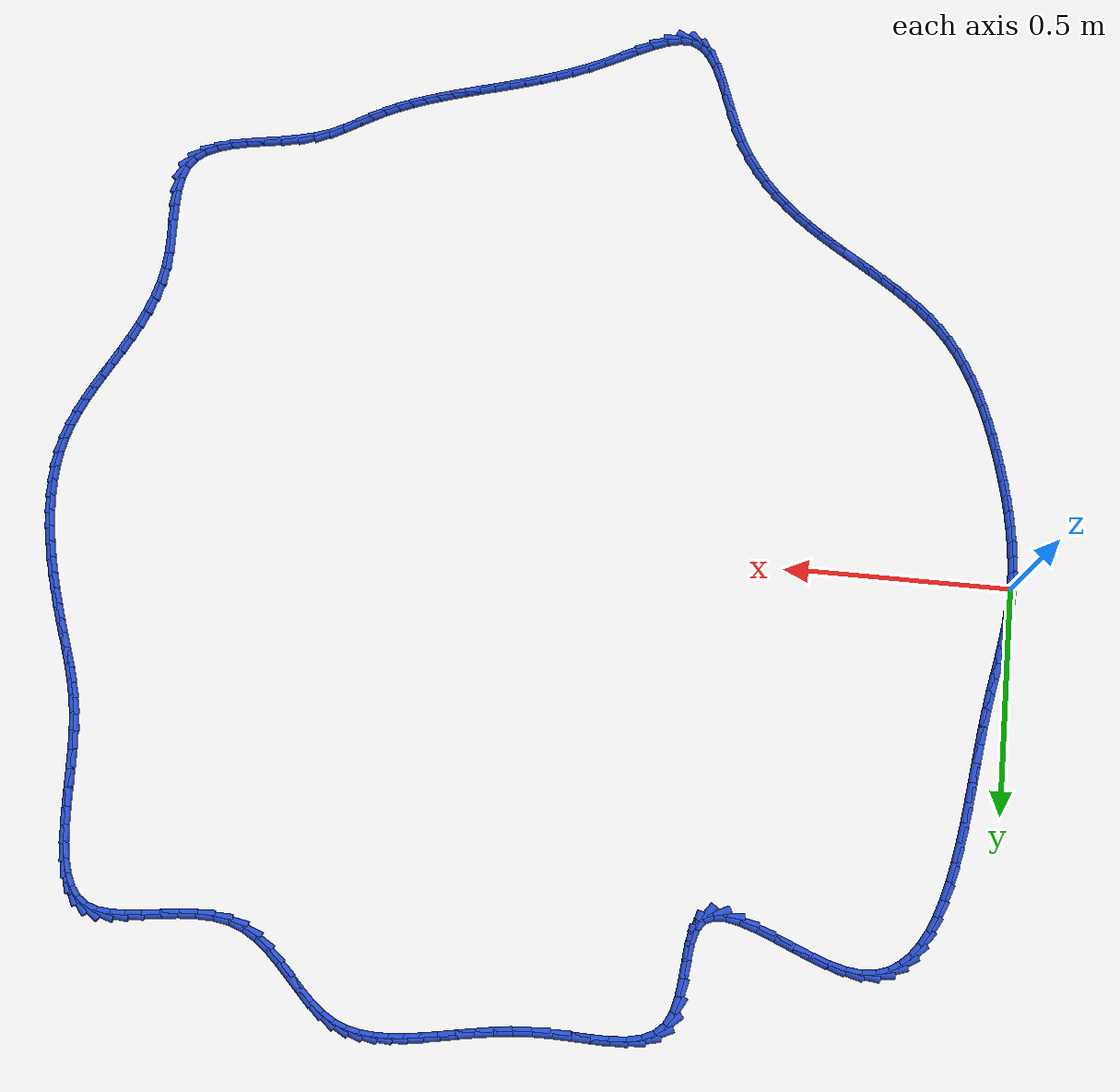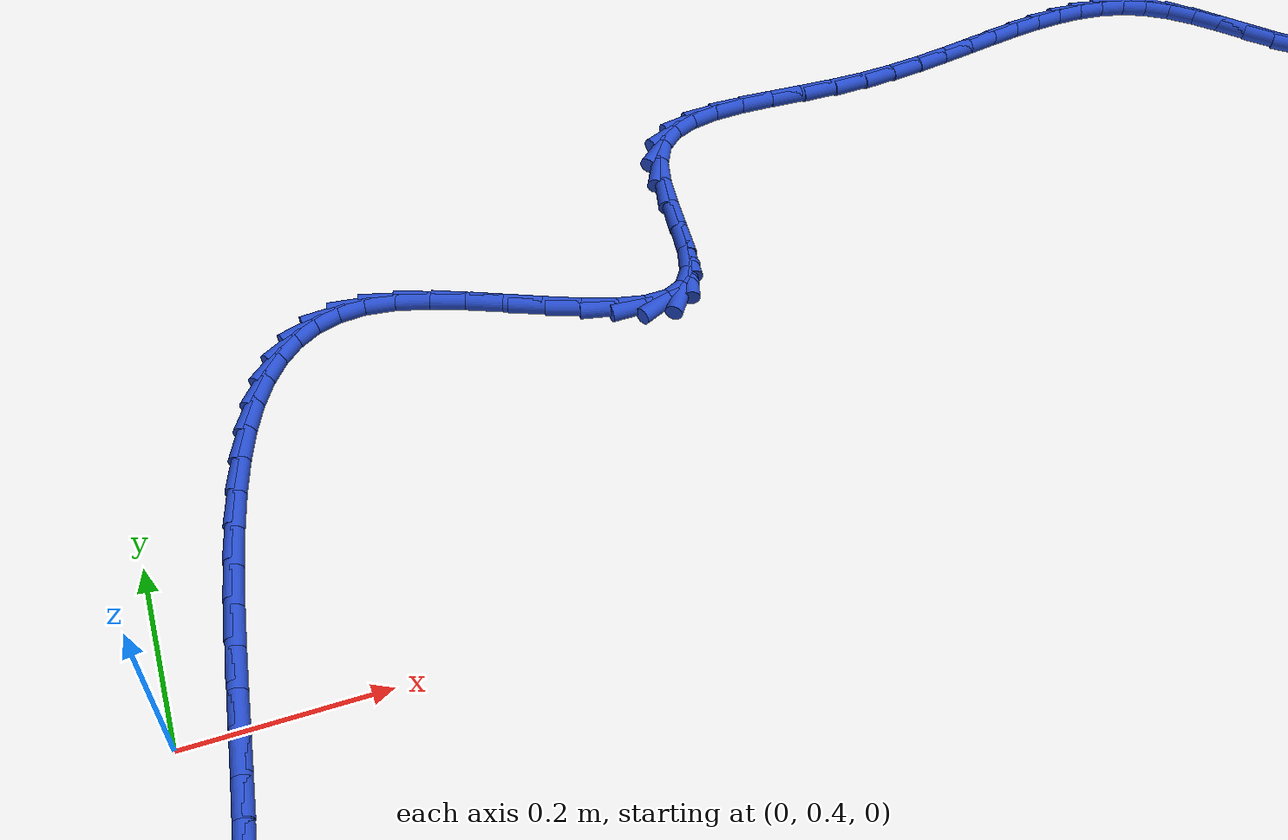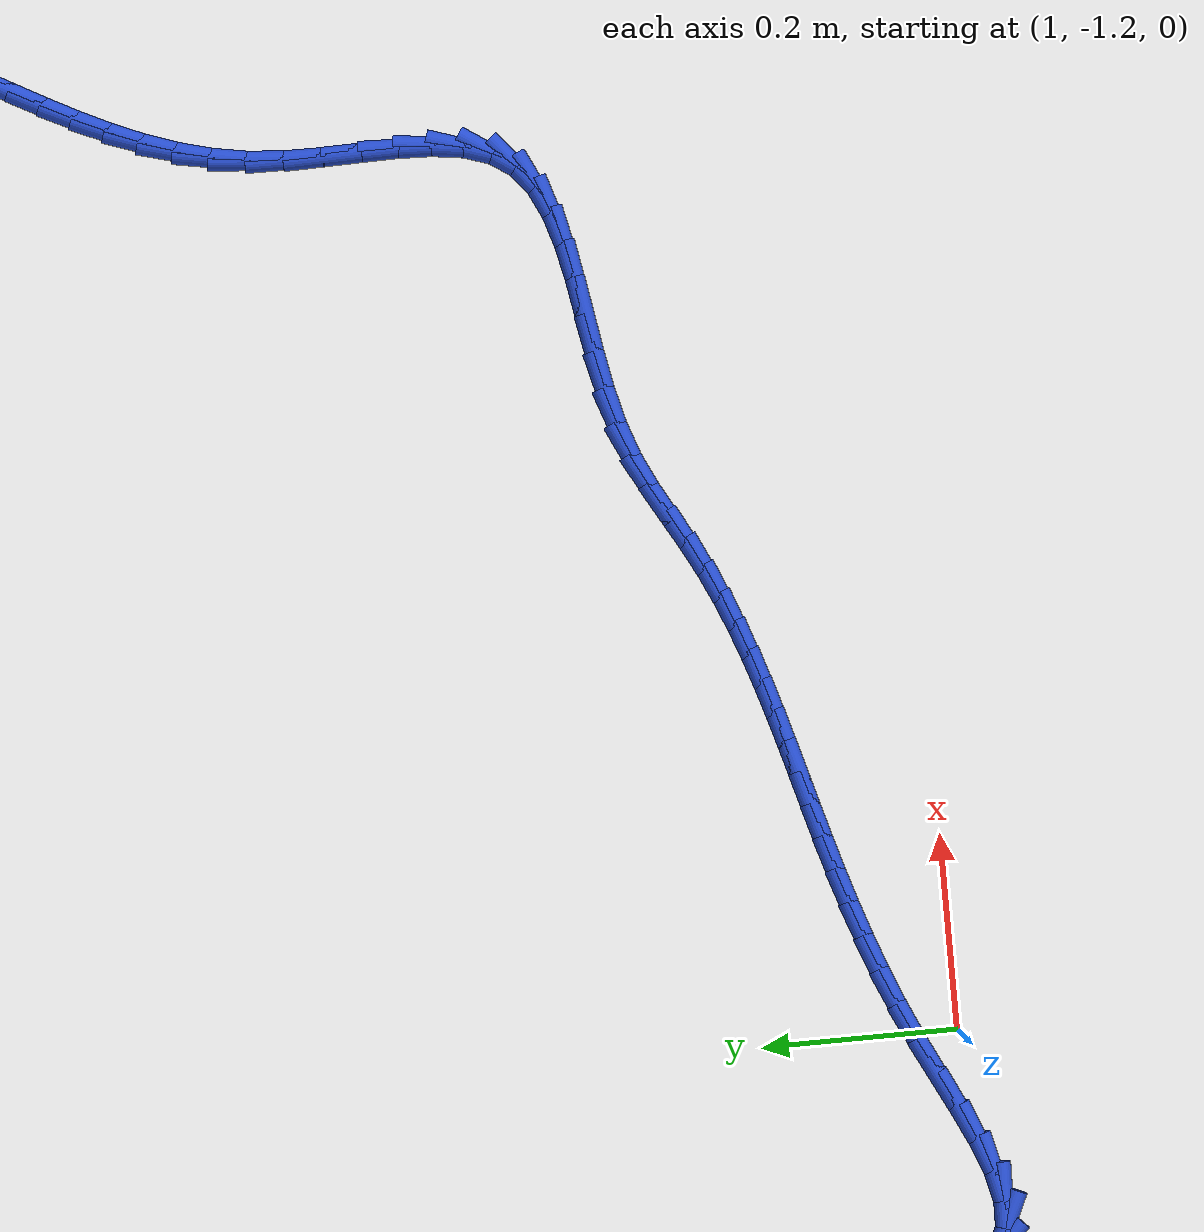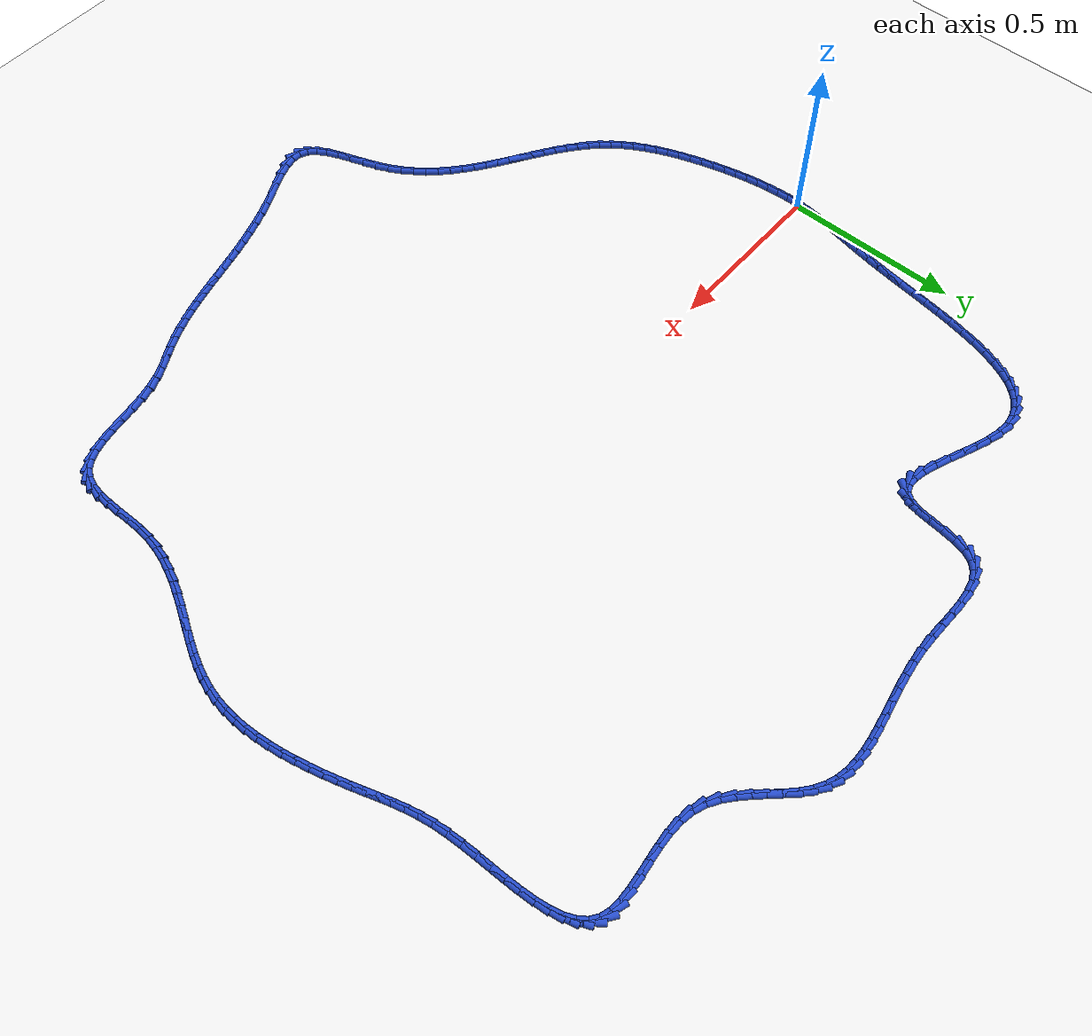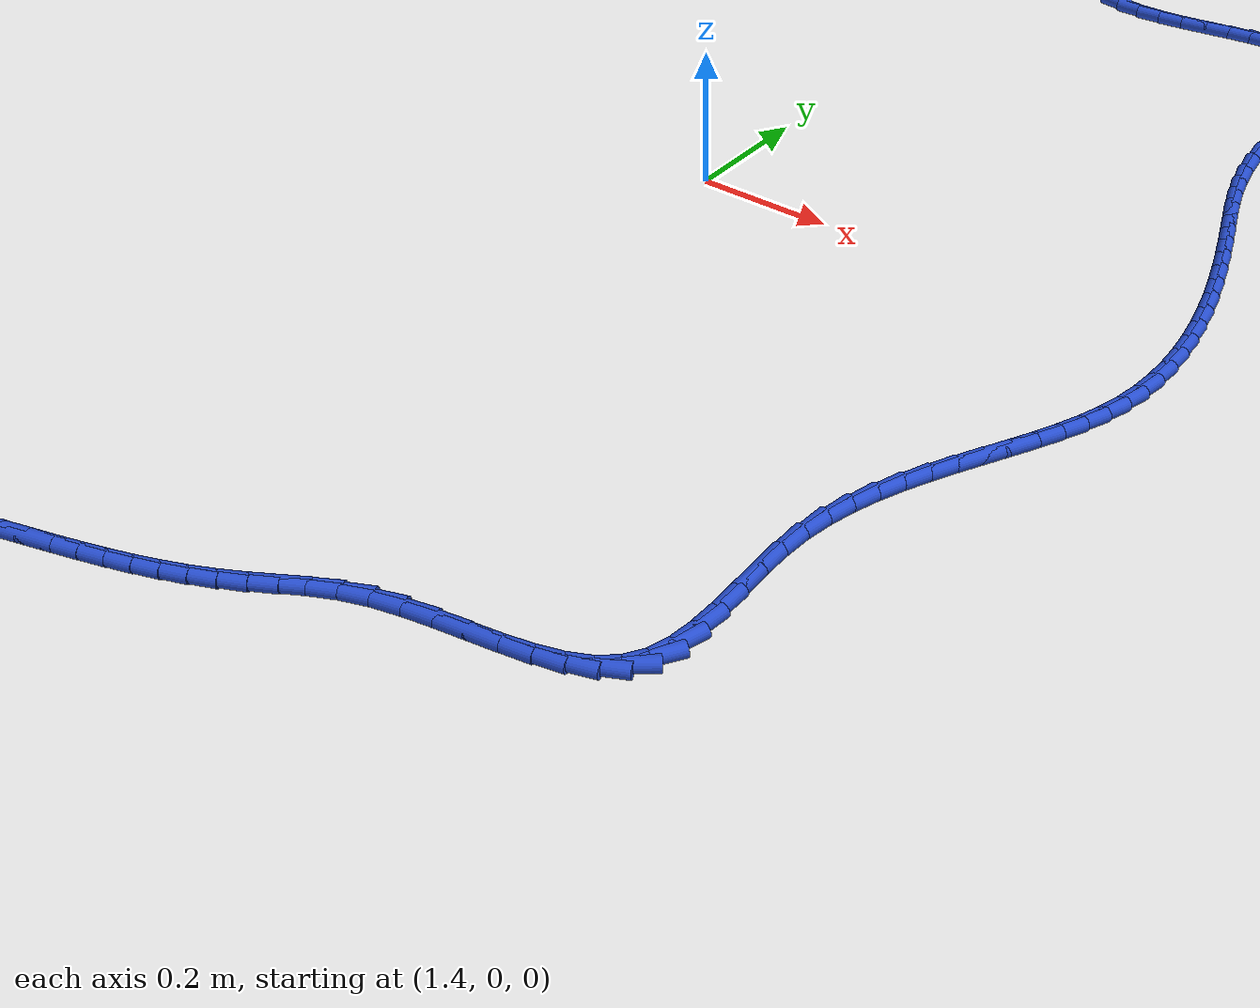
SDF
<sdf version="1.6">
 <world name="default">
  <light name="sun" type="directional">
   <pose>0 0 10 0 -0 0</pose>
   <diffuse>0.8 0.8 0.8 1</diffuse>
   <specular>0.2 0.2 0.2 1</specular>
   <attenuation>
    <range>1000</range>
    <constant>0.9</constant>
    <linear>0.01</linear>
    <quadratic>0.001</quadratic>
   </attenuation>
   <direction>-0.5 0.1 -0.9</direction>
  </light>
  <model name="ground_plane">
   <static>1</static>
   <link name="link">
    <collision name="collision">
     <geometry><plane><normal>0 0 1</normal><size>100 100</size></plane></geometry>
     <surface><friction><ode><mu>100</mu><mu2>50</mu2></ode></friction></surface>
    </collision>
    <visual name="visual">
     <cast_shadows>0</cast_shadows>
     <geometry><plane><normal>0 0 1</normal><size>100 100</size></plane></geometry>
     <material>
      <script><uri>file://media/materials/scripts/gazebo.material</uri><name>Gazebo/WhiteGlow</name></script>
     </material>
    </visual>
   </link>
  </model>
  <gravity>0 0 -9.8</gravity>
  <magnetic_field>6e-06 2.3e-05 -4.2e-05</magnetic_field>
  <atmosphere type="adiabatic"/>
  <physics name="default_physics" default="0" type="ode">
   <max_step_size>0.001</max_step_size>
   <real_time_factor>1</real_time_factor>
   <real_time_update_rate>1000</real_time_update_rate>
  </physics>
  <scene><ambient>0.4 0.4 0.4 1</ambient><background>0.7 0.7 0.7 1</background><shadows>1</shadows></scene>
  <spherical_coordinates>
   <surface_model>EARTH_WGS84</surface_model>
   <latitude_deg>0</latitude_deg>
   <longitude_deg>0</longitude_deg>
   <elevation>0</elevation>
   <heading_deg>0</heading_deg>
  </spherical_coordinates>
  <model name="line">
   <link name="link_0">
    <pose>1.734723475976807e-18 6.245004513516506e-17 0.01 0 1.57 1.516494529502316</pose>
    <collision name="collision">
     <geometry><cylinder><radius>0.01</radius><length>0.08</length></cylinder></geometry>
    </collision>
    <visual name="visual">
     <material>
      <script><name>Gazebo/Blue</name><uri>file://media/materials/scripts/gazebo.material</uri></script>
     </material>
     <geometry><cylinder><radius>0.01</radius><length>0.08</length></cylinder></geometry>
    </visual>
   </link>
   <link name="link_1">
    <pose>0.0017694688169561143 0.03255378939449071 0.01 0 1.57 1.4710826064364122</pose>
    <collision name="collision">
     <geometry><cylinder><radius>0.01</radius><length>0.08</length></cylinder></geometry>
    </collision>
    <visual name="visual">
     <material>
      <script><name>Gazebo/Blue</name><uri>file://media/materials/scripts/gazebo.material</uri></script>
     </material>
     <geometry><cylinder><radius>0.01</radius><length>0.08</length></cylinder></geometry>
    </visual>
   </link>
   <link name="link_2">
    <pose>0.004998973465190106 0.06483414226333158 0.01 0 1.57 1.4345876731881326</pose>
    <collision name="collision">
     <geometry><cylinder><radius>0.01</radius><length>0.08</length></cylinder></geometry>
    </collision>
    <visual name="visual">
     <material>
      <script><name>Gazebo/Blue</name><uri>file://media/materials/scripts/gazebo.material</uri></script>
     </material>
     <geometry><cylinder><radius>0.01</radius><length>0.08</length></cylinder></geometry>
    </visual>
   </link>
   <link name="link_3">
    <pose>0.009429887435138591 0.09716305787593267 0.01 0 1.57 1.4079163147194615</pose>
    <collision name="collision">
     <geometry><cylinder><radius>0.01</radius><length>0.08</length></cylinder></geometry>
    </collision>
    <visual name="visual">
     <material>
      <script><name>Gazebo/Blue</name><uri>file://media/materials/scripts/gazebo.material</uri></script>
     </material>
     <geometry><cylinder><radius>0.01</radius><length>0.08</length></cylinder></geometry>
    </visual>
   </link>
   <link name="link_4">
    <pose>0.014803584217238173 0.12986253550170396 0.01 0 1.57 1.3913320808936984</pose>
    <collision name="collision">
     <geometry><cylinder><radius>0.01</radius><length>0.08</length></cylinder></geometry>
    </collision>
    <visual name="visual">
     <material>
      <script><name>Gazebo/Blue</name><uri>file://media/materials/scripts/gazebo.material</uri></script>
     </material>
     <geometry><cylinder><radius>0.01</radius><length>0.08</length></cylinder></geometry>
    </visual>
   </link>
   <link name="link_5">
    <pose>0.020861437301925464 0.16325457441005548 0.01 0 1.57 1.3845459777414224</pose>
    <collision name="collision">
     <geometry><cylinder><radius>0.01</radius><length>0.08</length></cylinder></geometry>
    </collision>
    <visual name="visual">
     <material>
      <script><name>Gazebo/Blue</name><uri>file://media/materials/scripts/gazebo.material</uri></script>
     </material>
     <geometry><cylinder><radius>0.01</radius><length>0.08</length></cylinder></geometry>
    </visual>
   </link>
   <link name="link_6">
    <pose>0.027344820179637068 0.1976611738703972 0.01 0 1.57 1.3868421602056382</pose>
    <collision name="collision">
     <geometry><cylinder><radius>0.01</radius><length>0.08</length></cylinder></geometry>
    </collision>
    <visual name="visual">
     <material>
      <script><name>Gazebo/Blue</name><uri>file://media/materials/scripts/gazebo.material</uri></script>
     </material>
     <geometry><cylinder><radius>0.01</radius><length>0.08</length></cylinder></geometry>
    </visual>
   </link>
   <link name="link_7">
    <pose>0.0339951063408096 0.2334043331521391 0.01 0 1.57 1.397206629142584</pose>
    <collision name="collision">
     <geometry><cylinder><radius>0.01</radius><length>0.08</length></cylinder></geometry>
    </collision>
    <visual name="visual">
     <material>
      <script><name>Gazebo/Blue</name><uri>file://media/materials/scripts/gazebo.material</uri></script>
     </material>
     <geometry><cylinder><radius>0.01</radius><length>0.08</length></cylinder></geometry>
    </visual>
   </link>
   <link name="link_8">
    <pose>0.04055366927587964 0.27080605152469117 0.01 0 1.57 1.414296138216688</pose>
    <collision name="collision">
     <geometry><cylinder><radius>0.01</radius><length>0.08</length></cylinder></geometry>
    </collision>
    <visual name="visual">
     <material>
      <script><name>Gazebo/Blue</name><uri>file://media/materials/scripts/gazebo.material</uri></script>
     </material>
     <geometry><cylinder><radius>0.01</radius><length>0.08</length></cylinder></geometry>
    </visual>
   </link>
   <link name="link_9">
    <pose>0.04676655816186803 0.31018033766741737 0.01 0 1.57 1.431066428718873</pose>
    <collision name="collision">
     <geometry><cylinder><radius>0.01</radius><length>0.08</length></cylinder></geometry>
    </collision>
    <visual name="visual">
     <material>
      <script><name>Gazebo/Blue</name><uri>file://media/materials/scripts/gazebo.material</uri></script>
     </material>
     <geometry><cylinder><radius>0.01</radius><length>0.08</length></cylinder></geometry>
    </visual>
   </link>
   <link name="link_10">
    <pose>0.0525783032457674 0.3515020028319896 0.01 0 1.57 1.4401218542389516</pose>
    <collision name="collision">
     <geometry><cylinder><radius>0.01</radius><length>0.08</length></cylinder></geometry>
    </collision>
    <visual name="visual">
     <material>
      <script><name>Gazebo/Blue</name><uri>file://media/materials/scripts/gazebo.material</uri></script>
     </material>
     <geometry><cylinder><radius>0.01</radius><length>0.08</length></cylinder></geometry>
    </visual>
   </link>
   <link name="link_11">
    <pose>0.058201377449199135 0.3942879533121111 0.01 0 1.57 1.4419638176945608</pose>
    <collision name="collision">
     <geometry><cylinder><radius>0.01</radius><length>0.08</length></cylinder></geometry>
    </collision>
    <visual name="visual">
     <material>
      <script><name>Gazebo/Blue</name><uri>file://media/materials/scripts/gazebo.material</uri></script>
     </material>
     <geometry><cylinder><radius>0.01</radius><length>0.08</length></cylinder></geometry>
    </visual>
   </link>
   <link name="link_12">
    <pose>0.06386721503722509 0.4380226911076072 0.01 0 1.57 1.4371112335914393</pose>
    <collision name="collision">
     <geometry><cylinder><radius>0.01</radius><length>0.08</length></cylinder></geometry>
    </collision>
    <visual name="visual">
     <material>
      <script><name>Gazebo/Blue</name><uri>file://media/materials/scripts/gazebo.material</uri></script>
     </material>
     <geometry><cylinder><radius>0.01</radius><length>0.08</length></cylinder></geometry>
    </visual>
   </link>
   <link name="link_13">
    <pose>0.069807250274907 0.4821907182183031 0.01 0 1.57 1.4256176986108482</pose>
    <collision name="collision">
     <geometry><cylinder><radius>0.01</radius><length>0.08</length></cylinder></geometry>
    </collision>
    <visual name="visual">
     <material>
      <script><name>Gazebo/Blue</name><uri>file://media/materials/scripts/gazebo.material</uri></script>
     </material>
     <geometry><cylinder><radius>0.01</radius><length>0.08</length></cylinder></geometry>
    </visual>
   </link>
   <link name="link_14">
    <pose>0.07625291742730675 0.5262765366440245 0.01 0 1.57 1.4071086520204896</pose>
    <collision name="collision">
     <geometry><cylinder><radius>0.01</radius><length>0.08</length></cylinder></geometry>
    </collision>
    <visual name="visual">
     <material>
      <script><name>Gazebo/Blue</name><uri>file://media/materials/scripts/gazebo.material</uri></script>
     </material>
     <geometry><cylinder><radius>0.01</radius><length>0.08</length></cylinder></geometry>
    </visual>
   </link>
   <link name="link_15">
    <pose>0.08343565075948611 0.5697646483845966 0.01 0 1.57 1.3807576732418159</pose>
    <collision name="collision">
     <geometry><cylinder><radius>0.01</radius><length>0.08</length></cylinder></geometry>
    </collision>
    <visual name="visual">
     <material>
      <script><name>Gazebo/Blue</name><uri>file://media/materials/scripts/gazebo.material</uri></script>
     </material>
     <geometry><cylinder><radius>0.01</radius><length>0.08</length></cylinder></geometry>
    </visual>
   </link>
   <link name="link_16">
    <pose>0.09158688453650689 0.6121395554398449 0.01 0 1.57 1.3452048609490905</pose>
    <collision name="collision">
     <geometry><cylinder><radius>0.01</radius><length>0.08</length></cylinder></geometry>
    </collision>
    <visual name="visual">
     <material>
      <script><name>Gazebo/Blue</name><uri>file://media/materials/scripts/gazebo.material</uri></script>
     </material>
     <geometry><cylinder><radius>0.01</radius><length>0.08</length></cylinder></geometry>
    </visual>
   </link>
   <link name="link_17">
    <pose>0.10093805302343087 0.6528857598095943 0.01 0 1.57 1.2984128728582403</pose>
    <collision name="collision">
     <geometry><cylinder><radius>0.01</radius><length>0.08</length></cylinder></geometry>
    </collision>
    <visual name="visual">
     <material>
      <script><name>Gazebo/Blue</name><uri>file://media/materials/scripts/gazebo.material</uri></script>
     </material>
     <geometry><cylinder><radius>0.01</radius><length>0.08</length></cylinder></geometry>
    </visual>
   </link>
   <link name="link_18">
    <pose>0.11172059048531988 0.6914877634936708 0.01 0 1.57 1.237458272681989</pose>
    <collision name="collision">
     <geometry><cylinder><radius>0.01</radius><length>0.08</length></cylinder></geometry>
    </collision>
    <visual name="visual">
     <material>
      <script><name>Gazebo/Blue</name><uri>file://media/materials/scripts/gazebo.material</uri></script>
     </material>
     <geometry><cylinder><radius>0.01</radius><length>0.08</length></cylinder></geometry>
    </visual>
   </link>
   <link name="link_19">
    <pose>0.12416593118723575 0.7274300684918995 0.01 0 1.57 1.1582842394005377</pose>
    <collision name="collision">
     <geometry><cylinder><radius>0.01</radius><length>0.08</length></cylinder></geometry>
    </collision>
    <visual name="visual">
     <material>
      <script><name>Gazebo/Blue</name><uri>file://media/materials/scripts/gazebo.material</uri></script>
     </material>
     <geometry><cylinder><radius>0.01</radius><length>0.08</length></cylinder></geometry>
    </visual>
   </link>
   <link name="link_20">
    <pose>0.13850550939424022 0.760197176804106 0.01 0 1.57 1.0555437364735083</pose>
    <collision name="collision">
     <geometry><cylinder><radius>0.01</radius><length>0.08</length></cylinder></geometry>
    </collision>
    <visual name="visual">
     <material>
      <script><name>Gazebo/Blue</name><uri>file://media/materials/scripts/gazebo.material</uri></script>
     </material>
     <geometry><cylinder><radius>0.01</radius><length>0.08</length></cylinder></geometry>
    </visual>
   </link>
   <link name="link_21">
    <pose>0.15497075937139515 0.7892735904301154 0.01 0 1.57 0.9229427597832834</pose>
    <collision name="collision">
     <geometry><cylinder><radius>0.01</radius><length>0.08</length></cylinder></geometry>
    </collision>
    <visual name="visual">
     <material>
      <script><name>Gazebo/Blue</name><uri>file://media/materials/scripts/gazebo.material</uri></script>
     </material>
     <geometry><cylinder><radius>0.01</radius><length>0.08</length></cylinder></geometry>
    </visual>
   </link>
   <link name="link_22">
    <pose>0.17379311538376235 0.8141438113697528 0.01 0 1.57 0.7550325365634782</pose>
    <collision name="collision">
     <geometry><cylinder><radius>0.01</radius><length>0.08</length></cylinder></geometry>
    </collision>
    <visual name="visual">
     <material>
      <script><name>Gazebo/Blue</name><uri>file://media/materials/scripts/gazebo.material</uri></script>
     </material>
     <geometry><cylinder><radius>0.01</radius><length>0.08</length></cylinder></geometry>
    </visual>
   </link>
   <link name="link_23">
    <pose>0.19520401169640353 0.834292341622844 0.01 0 1.57 0.5516560724379624</pose>
    <collision name="collision">
     <geometry><cylinder><radius>0.01</radius><length>0.08</length></cylinder></geometry>
    </collision>
    <visual name="visual">
     <material>
      <script><name>Gazebo/Blue</name><uri>file://media/materials/scripts/gazebo.material</uri></script>
     </material>
     <geometry><cylinder><radius>0.01</radius><length>0.08</length></cylinder></geometry>
    </visual>
   </link>
   <link name="link_24">
    <pose>0.21943488257438062 0.8492036831892145 0.01 0 1.57 0.3238788285160609</pose>
    <collision name="collision">
     <geometry><cylinder><radius>0.01</radius><length>0.08</length></cylinder></geometry>
    </collision>
    <visual name="visual">
     <material>
      <script><name>Gazebo/Blue</name><uri>file://media/materials/scripts/gazebo.material</uri></script>
     </material>
     <geometry><cylinder><radius>0.01</radius><length>0.08</length></cylinder></geometry>
    </visual>
   </link>
   <link name="link_25">
    <pose>0.24671716228275534 0.8583623380686894 0.01 0 1.57 0.09428719234940389</pose>
    <collision name="collision">
     <geometry><cylinder><radius>0.01</radius><length>0.08</length></cylinder></geometry>
    </collision>
    <visual name="visual">
     <material>
      <script><name>Gazebo/Blue</name><uri>file://media/materials/scripts/gazebo.material</uri></script>
     </material>
     <geometry><cylinder><radius>0.01</radius><length>0.08</length></cylinder></geometry>
    </visual>
   </link>
   <link name="link_26">
    <pose>0.2772822850865895 0.861252808261094 0.01 0 1.57 -0.11207806475570599</pose>
    <collision name="collision">
     <geometry><cylinder><radius>0.01</radius><length>0.08</length></cylinder></geometry>
    </collision>
    <visual name="visual">
     <material>
      <script><name>Gazebo/Blue</name><uri>file://media/materials/scripts/gazebo.material</uri></script>
     </material>
     <geometry><cylinder><radius>0.01</radius><length>0.08</length></cylinder></geometry>
    </visual>
   </link>
   <link name="link_27">
    <pose>0.3113272808725779 0.8574210533799003 0.01 0 1.57 -0.25873900367864067</pose>
    <collision name="collision">
     <geometry><cylinder><radius>0.01</radius><length>0.08</length></cylinder></geometry>
    </collision>
    <visual name="visual">
     <material>
      <script><name>Gazebo/Blue</name><uri>file://media/materials/scripts/gazebo.material</uri></script>
     </material>
     <geometry><cylinder><radius>0.01</radius><length>0.08</length></cylinder></geometry>
    </visual>
   </link>
   <link name="link_28">
    <pose>0.34837616490626433 0.8476152600378117 0.01 0 1.57 -0.3434949601912979</pose>
    <collision name="collision">
     <geometry><cylinder><radius>0.01</radius><length>0.08</length></cylinder></geometry>
    </collision>
    <visual name="visual">
     <material>
      <script><name>Gazebo/Blue</name><uri>file://media/materials/scripts/gazebo.material</uri></script>
     </material>
     <geometry><cylinder><radius>0.01</radius><length>0.08</length></cylinder></geometry>
    </visual>
   </link>
   <link name="link_29">
    <pose>0.3873397503996484 0.8336789967925731 0.01 0 1.57 -0.386485069874754</pose>
    <collision name="collision">
     <geometry><cylinder><radius>0.01</radius><length>0.08</length></cylinder></geometry>
    </collision>
    <visual name="visual">
     <material>
      <script><name>Gazebo/Blue</name><uri>file://media/materials/scripts/gazebo.material</uri></script>
     </material>
     <geometry><cylinder><radius>0.01</radius><length>0.08</length></cylinder></geometry>
    </visual>
   </link>
   <link name="link_30">
    <pose>0.4271064411937049 0.8174958627600105 0.01 0 1.57 -0.39706691498467167</pose>
    <collision name="collision">
     <geometry><cylinder><radius>0.01</radius><length>0.08</length></cylinder></geometry>
    </collision>
    <visual name="visual">
     <material>
      <script><name>Gazebo/Blue</name><uri>file://media/materials/scripts/gazebo.material</uri></script>
     </material>
     <geometry><cylinder><radius>0.01</radius><length>0.08</length></cylinder></geometry>
    </visual>
   </link>
   <link name="link_31">
    <pose>0.466564641129408 0.8009494570559501 0.01 0 1.57 -0.37621189365036883</pose>
    <collision name="collision">
     <geometry><cylinder><radius>0.01</radius><length>0.08</length></cylinder></geometry>
    </collision>
    <visual name="visual">
     <material>
      <script><name>Gazebo/Blue</name><uri>file://media/materials/scripts/gazebo.material</uri></script>
     </material>
     <geometry><cylinder><radius>0.01</radius><length>0.08</length></cylinder></geometry>
    </visual>
   </link>
   <link name="link_32">
    <pose>0.5046027540477327 0.7859233787962181 0.01 0 1.57 -0.31633358657860455</pose>
    <collision name="collision">
     <geometry><cylinder><radius>0.01</radius><length>0.08</length></cylinder></geometry>
    </collision>
    <visual name="visual">
     <material>
      <script><name>Gazebo/Blue</name><uri>file://media/materials/scripts/gazebo.material</uri></script>
     </material>
     <geometry><cylinder><radius>0.01</radius><length>0.08</length></cylinder></geometry>
    </visual>
   </link>
   <link name="link_33">
    <pose>0.5401091837896534 0.7743012270966407 0.01 0 1.57 -0.19624844381312415</pose>
    <collision name="collision">
     <geometry><cylinder><radius>0.01</radius><length>0.08</length></cylinder></geometry>
    </collision>
    <visual name="visual">
     <material>
      <script><name>Gazebo/Blue</name><uri>file://media/materials/scripts/gazebo.material</uri></script>
     </material>
     <geometry><cylinder><radius>0.01</radius><length>0.08</length></cylinder></geometry>
    </visual>
   </link>
   <link name="link_34">
    <pose>0.5719723341961447 0.7679666010730446 0.01 0 1.57 0.030847902295947048</pose>
    <collision name="collision">
     <geometry><cylinder><radius>0.01</radius><length>0.08</length></cylinder></geometry>
    </collision>
    <visual name="visual">
     <material>
      <script><name>Gazebo/Blue</name><uri>file://media/materials/scripts/gazebo.material</uri></script>
     </material>
     <geometry><cylinder><radius>0.01</radius><length>0.08</length></cylinder></geometry>
    </visual>
   </link>
   <link name="link_35">
    <pose>0.5990806091081815 0.7688030998412557 0.01 0 1.57 0.43579109033403973</pose>
    <collision name="collision">
     <geometry><cylinder><radius>0.01</radius><length>0.08</length></cylinder></geometry>
    </collision>
    <visual name="visual">
     <material>
      <script><name>Gazebo/Blue</name><uri>file://media/materials/scripts/gazebo.material</uri></script>
     </material>
     <geometry><cylinder><radius>0.01</radius><length>0.08</length></cylinder></geometry>
    </visual>
   </link>
   <link name="link_36">
    <pose>0.6203224123667376 0.7786943225170999 0.01 0 1.57 0.9597044368736017</pose>
    <collision name="collision">
     <geometry><cylinder><radius>0.01</radius><length>0.08</length></cylinder></geometry>
    </collision>
    <visual name="visual">
     <material>
      <script><name>Gazebo/Blue</name><uri>file://media/materials/scripts/gazebo.material</uri></script>
     </material>
     <geometry><cylinder><radius>0.01</radius><length>0.08</length></cylinder></geometry>
    </visual>
   </link>
   <link name="link_37">
    <pose>0.6347462617645317 0.7992837804465411 0.01 0 1.57 1.2913432090761514</pose>
    <collision name="collision">
     <geometry><cylinder><radius>0.01</radius><length>0.08</length></cylinder></geometry>
    </collision>
    <visual name="visual">
     <material>
      <script><name>Gazebo/Blue</name><uri>file://media/materials/scripts/gazebo.material</uri></script>
     </material>
     <geometry><cylinder><radius>0.01</radius><length>0.08</length></cylinder></geometry>
    </visual>
   </link>
   <link name="link_38">
    <pose>0.643355238662773 0.8292841547567883 0.01 0 1.57 1.4305915507599878</pose>
    <collision name="collision">
     <geometry><cylinder><radius>0.01</radius><length>0.08</length></cylinder></geometry>
    </collision>
    <visual name="visual">
     <material>
      <script><name>Gazebo/Blue</name><uri>file://media/materials/scripts/gazebo.material</uri></script>
     </material>
     <geometry><cylinder><radius>0.01</radius><length>0.08</length></cylinder></geometry>
    </visual>
   </link>
   <link name="link_39">
    <pose>0.6484591666807342 0.8654486918655342 0.01 0 1.57 1.4704170810159158</pose>
    <collision name="collision">
     <geometry><cylinder><radius>0.01</radius><length>0.08</length></cylinder></geometry>
    </collision>
    <visual name="visual">
     <material>
      <script><name>Gazebo/Blue</name><uri>file://media/materials/scripts/gazebo.material</uri></script>
     </material>
     <geometry><cylinder><radius>0.01</radius><length>0.08</length></cylinder></geometry>
    </visual>
   </link>
   <link name="link_40">
    <pose>0.6523917985203208 0.9044947569944771 0.01 0 1.57 1.4397088436168461</pose>
    <collision name="collision">
     <geometry><cylinder><radius>0.01</radius><length>0.08</length></cylinder></geometry>
    </collision>
    <visual name="visual">
     <material>
      <script><name>Gazebo/Blue</name><uri>file://media/materials/scripts/gazebo.material</uri></script>
     </material>
     <geometry><cylinder><radius>0.01</radius><length>0.08</length></cylinder></geometry>
    </visual>
   </link>
   <link name="link_41">
    <pose>0.6574868868834388 0.9431397153653144 0.01 0 1.57 1.329833014490731</pose>
    <collision name="collision">
     <geometry><cylinder><radius>0.01</radius><length>0.08</length></cylinder></geometry>
    </collision>
    <visual name="visual">
     <material>
      <script><name>Gazebo/Blue</name><uri>file://media/materials/scripts/gazebo.material</uri></script>
     </material>
     <geometry><cylinder><radius>0.01</radius><length>0.08</length></cylinder></geometry>
    </visual>
   </link>
   <link name="link_42">
    <pose>0.6660781844719931 0.9781009321997431 0.01 0 1.57 1.0961474673463791</pose>
    <collision name="collision">
     <geometry><cylinder><radius>0.01</radius><length>0.08</length></cylinder></geometry>
    </collision>
    <visual name="visual">
     <material>
      <script><name>Gazebo/Blue</name><uri>file://media/materials/scripts/gazebo.material</uri></script>
     </material>
     <geometry><cylinder><radius>0.01</radius><length>0.08</length></cylinder></geometry>
    </visual>
   </link>
   <link name="link_43">
    <pose>0.6804781815162503 1.0061258585781676 0.01 0 1.57 0.7447042564367754</pose>
    <collision name="collision">
     <geometry><cylinder><radius>0.01</radius><length>0.08</length></cylinder></geometry>
    </collision>
    <visual name="visual">
     <material>
      <script><name>Gazebo/Blue</name><uri>file://media/materials/scripts/gazebo.material</uri></script>
     </material>
     <geometry><cylinder><radius>0.01</radius><length>0.08</length></cylinder></geometry>
    </visual>
   </link>
   <link name="link_44">
    <pose>0.701748521666757 1.0257318618023605 0.01 0 1.57 0.42750193804403613</pose>
    <collision name="collision">
     <geometry><cylinder><radius>0.01</radius><length>0.08</length></cylinder></geometry>
    </collision>
    <visual name="visual">
     <material>
      <script><name>Gazebo/Blue</name><uri>file://media/materials/scripts/gazebo.material</uri></script>
     </material>
     <geometry><cylinder><radius>0.01</radius><length>0.08</length></cylinder></geometry>
    </visual>
   </link>
   <link name="link_45">
    <pose>0.7290262209022123 1.0381596085712608 0.01 0 1.57 0.2054440767529333</pose>
    <collision name="collision">
     <geometry><cylinder><radius>0.01</radius><length>0.08</length></cylinder></geometry>
    </collision>
    <visual name="visual">
     <material>
      <script><name>Gazebo/Blue</name><uri>file://media/materials/scripts/gazebo.material</uri></script>
     </material>
     <geometry><cylinder><radius>0.01</radius><length>0.08</length></cylinder></geometry>
    </visual>
   </link>
   <link name="link_46">
    <pose>0.7612843826505585 1.0448816976905675 0.01 0 1.57 0.06862753163972198</pose>
    <collision name="collision">
     <geometry><cylinder><radius>0.01</radius><length>0.08</length></cylinder></geometry>
    </collision>
    <visual name="visual">
     <material>
      <script><name>Gazebo/Blue</name><uri>file://media/materials/scripts/gazebo.material</uri></script>
     </material>
     <geometry><cylinder><radius>0.01</radius><length>0.08</length></cylinder></geometry>
    </visual>
   </link>
   <link name="link_47">
    <pose>0.797496110339739 1.0473707279659812 0.01 0 1.57 -0.006935016039174146</pose>
    <collision name="collision">
     <geometry><cylinder><radius>0.01</radius><length>0.08</length></cylinder></geometry>
    </collision>
    <visual name="visual">
     <material>
      <script><name>Gazebo/Blue</name><uri>file://media/materials/scripts/gazebo.material</uri></script>
     </material>
     <geometry><cylinder><radius>0.01</radius><length>0.08</length></cylinder></geometry>
    </visual>
   </link>
   <link name="link_48">
    <pose>0.8366345073976962 1.0470992982032012 0.01 0 1.57 -0.03797784513476099</pose>
    <collision name="collision">
     <geometry><cylinder><radius>0.01</radius><length>0.08</length></cylinder></geometry>
    </collision>
    <visual name="visual">
     <material>
      <script><name>Gazebo/Blue</name><uri>file://media/materials/scripts/gazebo.material</uri></script>
     </material>
     <geometry><cylinder><radius>0.01</radius><length>0.08</length></cylinder></geometry>
    </visual>
   </link>
   <link name="link_49">
    <pose>0.8776726772523731 1.0455400072079277 0.01 0 1.57 -0.03278517306723285</pose>
    <collision name="collision">
     <geometry><cylinder><radius>0.01</radius><length>0.08</length></cylinder></geometry>
    </collision>
    <visual name="visual">
     <material>
      <script><name>Gazebo/Blue</name><uri>file://media/materials/scripts/gazebo.material</uri></script>
     </material>
     <geometry><cylinder><radius>0.01</radius><length>0.08</length></cylinder></geometry>
    </visual>
   </link>
   <link name="link_50">
    <pose>0.9195837233317121 1.04416545378586 0.01 0 1.57 0.006586137863566531</pose>
    <collision name="collision">
     <geometry><cylinder><radius>0.01</radius><length>0.08</length></cylinder></geometry>
    </collision>
    <visual name="visual">
     <material>
      <script><name>Gazebo/Blue</name><uri>file://media/materials/scripts/gazebo.material</uri></script>
     </material>
     <geometry><cylinder><radius>0.01</radius><length>0.08</length></cylinder></geometry>
    </visual>
   </link>
   <link name="link_51">
    <pose>0.9613443679664532 1.0444404991256073 0.01 0 1.57 0.06553168916651769</pose>
    <collision name="collision">
     <geometry><cylinder><radius>0.01</radius><length>0.08</length></cylinder></geometry>
    </collision>
    <visual name="visual">
     <material>
      <script><name>Gazebo/Blue</name><uri>file://media/materials/scripts/gazebo.material</uri></script>
     </material>
     <geometry><cylinder><radius>0.01</radius><length>0.08</length></cylinder></geometry>
    </visual>
   </link>
   <link name="link_52">
    <pose>1.0022607552886171 1.047125663928259 0.01 0 1.57 0.11453354054173945</pose>
    <collision name="collision">
     <geometry><cylinder><radius>0.01</radius><length>0.08</length></cylinder></geometry>
    </collision>
    <visual name="visual">
     <material>
      <script><name>Gazebo/Blue</name><uri>file://media/materials/scripts/gazebo.material</uri></script>
     </material>
     <geometry><cylinder><radius>0.01</radius><length>0.08</length></cylinder></geometry>
    </visual>
   </link>
   <link name="link_53">
    <pose>1.042227471189779 1.0517233148984595 0.01 0 1.57 0.14980049710011215</pose>
    <collision name="collision">
     <geometry><cylinder><radius>0.01</radius><length>0.08</length></cylinder></geometry>
    </collision>
    <visual name="visual">
     <material>
      <script><name>Gazebo/Blue</name><uri>file://media/materials/scripts/gazebo.material</uri></script>
     </material>
     <geometry><cylinder><radius>0.01</radius><length>0.08</length></cylinder></geometry>
    </visual>
   </link>
   <link name="link_54">
    <pose>1.0812000555044328 1.057605492424545 0.01 0 1.57 0.1706942739636232</pose>
    <collision name="collision">
     <geometry><cylinder><radius>0.01</radius><length>0.08</length></cylinder></geometry>
    </collision>
    <visual name="visual">
     <material>
      <script><name>Gazebo/Blue</name><uri>file://media/materials/scripts/gazebo.material</uri></script>
     </material>
     <geometry><cylinder><radius>0.01</radius><length>0.08</length></cylinder></geometry>
    </visual>
   </link>
   <link name="link_55">
    <pose>1.1191340480670742 1.0641442368948526 0.01 0 1.57 0.17636240588154645</pose>
    <collision name="collision">
     <geometry><cylinder><radius>0.01</radius><length>0.08</length></cylinder></geometry>
    </collision>
    <visual name="visual">
     <material>
      <script><name>Gazebo/Blue</name><uri>file://media/materials/scripts/gazebo.material</uri></script>
     </material>
     <geometry><cylinder><radius>0.01</radius><length>0.08</length></cylinder></geometry>
    </visual>
   </link>
   <link name="link_56">
    <pose>1.1559849887121985 1.070711588697717 0.01 0 1.57 0.16553254162809372</pose>
    <collision name="collision">
     <geometry><cylinder><radius>0.01</radius><length>0.08</length></cylinder></geometry>
    </collision>
    <visual name="visual">
     <material>
      <script><name>Gazebo/Blue</name><uri>file://media/materials/scripts/gazebo.material</uri></script>
     </material>
     <geometry><cylinder><radius>0.01</radius><length>0.08</length></cylinder></geometry>
    </visual>
   </link>
   <link name="link_57">
    <pose>1.1917084172743004 1.0766795882214741 0.01 0 1.57 0.13635518921580084</pose>
    <collision name="collision">
     <geometry><cylinder><radius>0.01</radius><length>0.08</length></cylinder></geometry>
    </collision>
    <visual name="visual">
     <material>
      <script><name>Gazebo/Blue</name><uri>file://media/materials/scripts/gazebo.material</uri></script>
     </material>
     <geometry><cylinder><radius>0.01</radius><length>0.08</length></cylinder></geometry>
    </visual>
   </link>
   <link name="link_58">
    <pose>1.2262598735878751 1.08142027585446 0.01 0 1.57 0.08634288738757968</pose>
    <collision name="collision">
     <geometry><cylinder><radius>0.01</radius><length>0.08</length></cylinder></geometry>
    </collision>
    <visual name="visual">
     <material>
      <script><name>Gazebo/Blue</name><uri>file://media/materials/scripts/gazebo.material</uri></script>
     </material>
     <geometry><cylinder><radius>0.01</radius><length>0.08</length></cylinder></geometry>
    </visual>
   </link>
   <link name="link_59">
    <pose>1.2595948974874176 1.0843056919850103 0.01 0 1.57 0.012538576199997879</pose>
    <collision name="collision">
     <geometry><cylinder><radius>0.01</radius><length>0.08</length></cylinder></geometry>
    </collision>
    <visual name="visual">
     <material>
      <script><name>Gazebo/Blue</name><uri>file://media/materials/scripts/gazebo.material</uri></script>
     </material>
     <geometry><cylinder><radius>0.01</radius><length>0.08</length></cylinder></geometry>
    </visual>
   </link>
   <link name="link_60">
    <pose>1.2916690288074235 1.0847078770014613 0.01 0 1.57 -0.08781753367430056</pose>
    <collision name="collision">
     <geometry><cylinder><radius>0.01</radius><length>0.08</length></cylinder></geometry>
    </collision>
    <visual name="visual">
     <material>
      <script><name>Gazebo/Blue</name><uri>file://media/materials/scripts/gazebo.material</uri></script>
     </material>
     <geometry><cylinder><radius>0.01</radius><length>0.08</length></cylinder></geometry>
    </visual>
   </link>
   <link name="link_61">
    <pose>1.3224378073823875 1.0819988712921487 0.01 0 1.57 -0.2157715016408034</pose>
    <collision name="collision">
     <geometry><cylinder><radius>0.01</radius><length>0.08</length></cylinder></geometry>
    </collision>
    <visual name="visual">
     <material>
      <script><name>Gazebo/Blue</name><uri>file://media/materials/scripts/gazebo.material</uri></script>
     </material>
     <geometry><cylinder><radius>0.01</radius><length>0.08</length></cylinder></geometry>
    </visual>
   </link>
   <link name="link_62">
    <pose>1.3518567730468045 1.0755507152454085 0.01 0 1.57 -0.36830910587126237</pose>
    <collision name="collision">
     <geometry><cylinder><radius>0.01</radius><length>0.08</length></cylinder></geometry>
    </collision>
    <visual name="visual">
     <material>
      <script><name>Gazebo/Blue</name><uri>file://media/materials/scripts/gazebo.material</uri></script>
     </material>
     <geometry><cylinder><radius>0.01</radius><length>0.08</length></cylinder></geometry>
    </visual>
   </link>
   <link name="link_63">
    <pose>1.3798814656351701 1.0647354492495755 0.01 0 1.57 -0.5361514295140511</pose>
    <collision name="collision">
     <geometry><cylinder><radius>0.01</radius><length>0.08</length></cylinder></geometry>
    </collision>
    <visual name="visual">
     <material>
      <script><name>Gazebo/Blue</name><uri>file://media/materials/scripts/gazebo.material</uri></script>
     </material>
     <geometry><cylinder><radius>0.01</radius><length>0.08</length></cylinder></geometry>
    </visual>
   </link>
   <link name="link_64">
    <pose>1.4064705342691812 1.0489359530508424 0.01 0 1.57 -0.6835282698975131</pose>
    <collision name="collision">
     <geometry><cylinder><radius>0.01</radius><length>0.08</length></cylinder></geometry>
    </collision>
    <visual name="visual">
     <material>
      <script><name>Gazebo/Blue</name><uri>file://media/materials/scripts/gazebo.material</uri></script>
     </material>
     <geometry><cylinder><radius>0.01</radius><length>0.08</length></cylinder></geometry>
    </visual>
   </link>
   <link name="link_65">
    <pose>1.4318027592517677 1.0283025107852333 0.01 0 1.57 -0.7738669091790529</pose>
    <collision name="collision">
     <geometry><cylinder><radius>0.01</radius><length>0.08</length></cylinder></geometry>
    </collision>
    <visual name="visual">
     <material>
      <script><name>Gazebo/Blue</name><uri>file://media/materials/scripts/gazebo.material</uri></script>
     </material>
     <geometry><cylinder><radius>0.01</radius><length>0.08</length></cylinder></geometry>
    </visual>
   </link>
   <link name="link_66">
    <pose>1.4564189722497611 1.0042475622018368 0.01 0 1.57 -0.8145786219902336</pose>
    <collision name="collision">
     <geometry><cylinder><radius>0.01</radius><length>0.08</length></cylinder></geometry>
    </collision>
    <visual name="visual">
     <material>
      <script><name>Gazebo/Blue</name><uri>file://media/materials/scripts/gazebo.material</uri></script>
     </material>
     <geometry><cylinder><radius>0.01</radius><length>0.08</length></cylinder></geometry>
    </visual>
   </link>
   <link name="link_67">
    <pose>1.4808937200480372 0.9783010821006533 0.01 0 1.57 -0.8127306843363291</pose>
    <collision name="collision">
     <geometry><cylinder><radius>0.01</radius><length>0.08</length></cylinder></geometry>
    </collision>
    <visual name="visual">
     <material>
      <script><name>Gazebo/Blue</name><uri>file://media/materials/scripts/gazebo.material</uri></script>
     </material>
     <geometry><cylinder><radius>0.01</radius><length>0.08</length></cylinder></geometry>
    </visual>
   </link>
   <link name="link_68">
    <pose>1.5058015494314747 0.9519930452816853 0.01 0 1.57 -0.770203213964623</pose>
    <collision name="collision">
     <geometry><cylinder><radius>0.01</radius><length>0.08</length></cylinder></geometry>
    </collision>
    <visual name="visual">
     <material>
      <script><name>Gazebo/Blue</name><uri>file://media/materials/scripts/gazebo.material</uri></script>
     </material>
     <geometry><cylinder><radius>0.01</radius><length>0.08</length></cylinder></geometry>
    </visual>
   </link>
   <link name="link_69">
    <pose>1.5317170071849522 0.9268534265449336 0.01 0 1.57 -0.6844901062890572</pose>
    <collision name="collision">
     <geometry><cylinder><radius>0.01</radius><length>0.08</length></cylinder></geometry>
    </collision>
    <visual name="visual">
     <material>
      <script><name>Gazebo/Blue</name><uri>file://media/materials/scripts/gazebo.material</uri></script>
     </material>
     <geometry><cylinder><radius>0.01</radius><length>0.08</length></cylinder></geometry>
    </visual>
   </link>
   <link name="link_70">
    <pose>1.5592146400933464 0.9044122006904004 0.01 0 1.57 -0.5507745719869069</pose>
    <collision name="collision">
     <geometry><cylinder><radius>0.01</radius><length>0.08</length></cylinder></geometry>
    </collision>
    <visual name="visual">
     <material>
      <script><name>Gazebo/Blue</name><uri>file://media/materials/scripts/gazebo.material</uri></script>
     </material>
     <geometry><cylinder><radius>0.01</radius><length>0.08</length></cylinder></geometry>
    </visual>
   </link>
   <link name="link_71">
    <pose>1.5888689949415364 0.8861993425180869 0.01 0 1.57 -0.3674892081311739</pose>
    <collision name="collision">
     <geometry><cylinder><radius>0.01</radius><length>0.08</length></cylinder></geometry>
    </collision>
    <visual name="visual">
     <material>
      <script><name>Gazebo/Blue</name><uri>file://media/materials/scripts/gazebo.material</uri></script>
     </material>
     <geometry><cylinder><radius>0.01</radius><length>0.08</length></cylinder></geometry>
    </visual>
   </link>
   <link name="link_72">
    <pose>1.6212491632657005 0.8737337076962128 0.01 0 1.57 -0.17479285689291793</pose>
    <collision name="collision">
     <geometry><cylinder><radius>0.01</radius><length>0.08</length></cylinder></geometry>
    </collision>
    <visual name="visual">
     <material>
      <script><name>Gazebo/Blue</name><uri>file://media/materials/scripts/gazebo.material</uri></script>
     </material>
     <geometry><cylinder><radius>0.01</radius><length>0.08</length></cylinder></geometry>
    </visual>
   </link>
   <link name="link_73">
    <pose>1.6564273681421782 0.8675214123850711 0.01 0 1.57 -0.033953131991459135</pose>
    <collision name="collision">
     <geometry><cylinder><radius>0.01</radius><length>0.08</length></cylinder></geometry>
    </collision>
    <visual name="visual">
     <material>
      <script><name>Gazebo/Blue</name><uri>file://media/materials/scripts/gazebo.material</uri></script>
     </material>
     <geometry><cylinder><radius>0.01</radius><length>0.08</length></cylinder></geometry>
    </visual>
   </link>
   <link name="link_74">
    <pose>1.6935881230223038 0.8662592033011823 0.01 0 1.57 0.05740015635863599</pose>
    <collision name="collision">
     <geometry><cylinder><radius>0.01</radius><length>0.08</length></cylinder></geometry>
    </collision>
    <visual name="visual">
     <material>
      <script><name>Gazebo/Blue</name><uri>file://media/materials/scripts/gazebo.material</uri></script>
     </material>
     <geometry><cylinder><radius>0.01</radius><length>0.08</length></cylinder></geometry>
    </visual>
   </link>
   <link name="link_75">
    <pose>1.7318239666912238 0.8684563602846068 0.01 0 1.57 0.10805215866762681</pose>
    <collision name="collision">
     <geometry><cylinder><radius>0.01</radius><length>0.08</length></cylinder></geometry>
    </collision>
    <visual name="visual">
     <material>
      <script><name>Gazebo/Blue</name><uri>file://media/materials/scripts/gazebo.material</uri></script>
     </material>
     <geometry><cylinder><radius>0.01</radius><length>0.08</length></cylinder></geometry>
    </visual>
   </link>
   <link name="link_76">
    <pose>1.7702274379340859 0.8726221631754058 0.01 0 1.57 0.12267562451456339</pose>
    <collision name="collision">
     <geometry><cylinder><radius>0.01</radius><length>0.08</length></cylinder></geometry>
    </collision>
    <visual name="visual">
     <material>
      <script><name>Gazebo/Blue</name><uri>file://media/materials/scripts/gazebo.material</uri></script>
     </material>
     <geometry><cylinder><radius>0.01</radius><length>0.08</length></cylinder></geometry>
    </visual>
   </link>
   <link name="link_77">
    <pose>1.8078910755360351 0.8772658918136395 0.01 0 1.57 0.10047405103115307</pose>
    <collision name="collision">
     <geometry><cylinder><radius>0.01</radius><length>0.08</length></cylinder></geometry>
    </collision>
    <visual name="visual">
     <material>
      <script><name>Gazebo/Blue</name><uri>file://media/materials/scripts/gazebo.material</uri></script>
     </material>
     <geometry><cylinder><radius>0.01</radius><length>0.08</length></cylinder></geometry>
    </visual>
   </link>
   <link name="link_78">
    <pose>1.8439074182822188 0.8808968260393691 0.01 0 1.57 0.03368021167997193</pose>
    <collision name="collision">
     <geometry><cylinder><radius>0.01</radius><length>0.08</length></cylinder></geometry>
    </collision>
    <visual name="visual">
     <material>
      <script><name>Gazebo/Blue</name><uri>file://media/materials/scripts/gazebo.material</uri></script>
     </material>
     <geometry><cylinder><radius>0.01</radius><length>0.08</length></cylinder></geometry>
    </visual>
   </link>
   <link name="link_79">
    <pose>1.877369004957784 0.8820242456926554 0.01 0 1.57 -0.09527319654171025</pose>
    <collision name="collision">
     <geometry><cylinder><radius>0.01</radius><length>0.08</length></cylinder></geometry>
    </collision>
    <visual name="visual">
     <material>
      <script><name>Gazebo/Blue</name><uri>file://media/materials/scripts/gazebo.material</uri></script>
     </material>
     <geometry><cylinder><radius>0.01</radius><length>0.08</length></cylinder></geometry>
    </visual>
   </link>
   <link name="link_80">
    <pose>1.9073683743478758 0.8791574306135586 0.01 0 1.57 -0.3150123258118781</pose>
    <collision name="collision">
     <geometry><cylinder><radius>0.01</radius><length>0.08</length></cylinder></geometry>
    </collision>
    <visual name="visual">
     <material>
      <script><name>Gazebo/Blue</name><uri>file://media/materials/scripts/gazebo.material</uri></script>
     </material>
     <geometry><cylinder><radius>0.01</radius><length>0.08</length></cylinder></geometry>
    </visual>
   </link>
   <link name="link_81">
    <pose>1.9329980652376415 0.8708056606421397 0.01 0 1.57 -0.6276441172366608</pose>
    <collision name="collision">
     <geometry><cylinder><radius>0.01</radius><length>0.08</length></cylinder></geometry>
    </collision>
    <visual name="visual">
     <material>
      <script><name>Gazebo/Blue</name><uri>file://media/materials/scripts/gazebo.material</uri></script>
     </material>
     <geometry><cylinder><radius>0.01</radius><length>0.08</length></cylinder></geometry>
    </visual>
   </link>
   <link name="link_82">
    <pose>1.953603747276751 0.855855978271142 0.01 0 1.57 -0.9238707753283545</pose>
    <collision name="collision">
     <geometry><cylinder><radius>0.01</radius><length>0.08</length></cylinder></geometry>
    </collision>
    <visual name="visual">
     <material>
      <script><name>Gazebo/Blue</name><uri>file://media/materials/scripts/gazebo.material</uri></script>
     </material>
     <geometry><cylinder><radius>0.01</radius><length>0.08</length></cylinder></geometry>
    </visual>
   </link>
   <link name="link_83">
    <pose>1.969560403234466 0.8347315328415676 0.01 0 1.57 -1.1471370626614341</pose>
    <collision name="collision">
     <geometry><cylinder><radius>0.01</radius><length>0.08</length></cylinder></geometry>
    </collision>
    <visual name="visual">
     <material>
      <script><name>Gazebo/Blue</name><uri>file://media/materials/scripts/gazebo.material</uri></script>
     </material>
     <geometry><cylinder><radius>0.01</radius><length>0.08</length></cylinder></geometry>
    </visual>
   </link>
   <link name="link_84">
    <pose>1.9815046109428123 0.8082458679872039 0.01 0 1.57 -1.3014067844544501</pose>
    <collision name="collision">
     <geometry><cylinder><radius>0.01</radius><length>0.08</length></cylinder></geometry>
    </collision>
    <visual name="visual">
     <material>
      <script><name>Gazebo/Blue</name><uri>file://media/materials/scripts/gazebo.material</uri></script>
     </material>
     <geometry><cylinder><radius>0.01</radius><length>0.08</length></cylinder></geometry>
    </visual>
   </link>
   <link name="link_85">
    <pose>1.9900729482762098 0.7772125274051065 0.01 0 1.57 -1.4046832667005207</pose>
    <collision name="collision">
     <geometry><cylinder><radius>0.01</radius><length>0.08</length></cylinder></geometry>
    </collision>
    <visual name="visual">
     <material>
      <script><name>Gazebo/Blue</name><uri>file://media/materials/scripts/gazebo.material</uri></script>
     </material>
     <geometry><cylinder><radius>0.01</radius><length>0.08</length></cylinder></geometry>
    </visual>
   </link>
   <link name="link_86">
    <pose>1.9959019931090765 0.7424450547923308 0.01 0 1.57 -1.4722436778712604</pose>
    <collision name="collision">
     <geometry><cylinder><radius>0.01</radius><length>0.08</length></cylinder></geometry>
    </collision>
    <visual name="visual">
     <material>
      <script><name>Gazebo/Blue</name><uri>file://media/materials/scripts/gazebo.material</uri></script>
     </material>
     <geometry><cylinder><radius>0.01</radius><length>0.08</length></cylinder></geometry>
    </visual>
   </link>
   <link name="link_87">
    <pose>1.9996283233158325 0.7047569938459319 0.01 0 1.57 -1.514061513928751</pose>
    <collision name="collision">
     <geometry><cylinder><radius>0.01</radius><length>0.08</length></cylinder></geometry>
    </collision>
    <visual name="visual">
     <material>
      <script><name>Gazebo/Blue</name><uri>file://media/materials/scripts/gazebo.material</uri></script>
     </material>
     <geometry><cylinder><radius>0.01</radius><length>0.08</length></cylinder></geometry>
    </visual>
   </link>
   <link name="link_88">
    <pose>2.001888516770897 0.6649618882629648 0.01 0 1.57 -1.535992107485634</pose>
    <collision name="collision">
     <geometry><cylinder><radius>0.01</radius><length>0.08</length></cylinder></geometry>
    </collision>
    <visual name="visual">
     <material>
      <script><name>Gazebo/Blue</name><uri>file://media/materials/scripts/gazebo.material</uri></script>
     </material>
     <geometry><cylinder><radius>0.01</radius><length>0.08</length></cylinder></geometry>
    </visual>
   </link>
   <link name="link_89">
    <pose>2.0033191513486885 0.6238732817404853 0.01 0 1.57 -1.5410313327814171</pose>
    <collision name="collision">
     <geometry><cylinder><radius>0.01</radius><length>0.08</length></cylinder></geometry>
    </collision>
    <visual name="visual">
     <material>
      <script><name>Gazebo/Blue</name><uri>file://media/materials/scripts/gazebo.material</uri></script>
     </material>
     <geometry><cylinder><radius>0.01</radius><length>0.08</length></cylinder></geometry>
    </visual>
   </link>
   <link name="link_90">
    <pose>2.0045568049236273 0.5823047179755485 0.01 0 1.57 -1.5300464621870478</pose>
    <collision name="collision">
     <geometry><cylinder><radius>0.01</radius><length>0.08</length></cylinder></geometry>
    </collision>
    <visual name="visual">
     <material>
      <script><name>Gazebo/Blue</name><uri>file://media/materials/scripts/gazebo.material</uri></script>
     </material>
     <geometry><cylinder><radius>0.01</radius><length>0.08</length></cylinder></geometry>
    </visual>
   </link>
   <link name="link_91">
    <pose>2.0062380553701327 0.5410697406652095 0.01 0 1.57 -1.5020206234922826</pose>
    <collision name="collision">
     <geometry><cylinder><radius>0.01</radius><length>0.08</length></cylinder></geometry>
    </collision>
    <visual name="visual">
     <material>
      <script><name>Gazebo/Blue</name><uri>file://media/materials/scripts/gazebo.material</uri></script>
     </material>
     <geometry><cylinder><radius>0.01</radius><length>0.08</length></cylinder></geometry>
    </visual>
   </link>
   <link name="link_92">
    <pose>2.008999480562623 0.500981893506523 0.01 0 1.57 -1.4539474165723336</pose>
    <collision name="collision">
     <geometry><cylinder><radius>0.01</radius><length>0.08</length></cylinder></geometry>
    </collision>
    <visual name="visual">
     <material>
      <script><name>Gazebo/Blue</name><uri>file://media/materials/scripts/gazebo.material</uri></script>
     </material>
     <geometry><cylinder><radius>0.01</radius><length>0.08</length></cylinder></geometry>
    </visual>
   </link>
   <link name="link_93">
    <pose>2.013475353188538 0.4628515989381514 0.01 0 1.57 -1.3910265826286867</pose>
    <collision name="collision">
     <geometry><cylinder><radius>0.01</radius><length>0.08</length></cylinder></geometry>
    </collision>
    <visual name="visual">
     <material>
      <script><name>Gazebo/Blue</name><uri>file://media/materials/scripts/gazebo.material</uri></script>
     </material>
     <geometry><cylinder><radius>0.01</radius><length>0.08</length></cylinder></geometry>
    </visual>
   </link>
   <link name="link_94">
    <pose>2.019980428911793 0.4270566484668012 0.01 0 1.57 -1.3336770683223065</pose>
    <collision name="collision">
     <geometry><cylinder><radius>0.01</radius><length>0.08</length></cylinder></geometry>
    </collision>
    <visual name="visual">
     <material>
      <script><name>Gazebo/Blue</name><uri>file://media/materials/scripts/gazebo.material</uri></script>
     </material>
     <geometry><cylinder><radius>0.01</radius><length>0.08</length></cylinder></geometry>
    </visual>
   </link>
   <link name="link_95">
    <pose>2.0281857879008784 0.393103287143242 0.01 0 1.57 -1.2881586921767574</pose>
    <collision name="collision">
     <geometry><cylinder><radius>0.01</radius><length>0.08</length></cylinder></geometry>
    </collision>
    <visual name="visual">
     <material>
      <script><name>Gazebo/Blue</name><uri>file://media/materials/scripts/gazebo.material</uri></script>
     </material>
     <geometry><cylinder><radius>0.01</radius><length>0.08</length></cylinder></geometry>
    </visual>
   </link>
   <link name="link_96">
    <pose>2.0376852229975144 0.3603931117968773 0.01 0 1.57 -1.2575223088086525</pose>
    <collision name="collision">
     <geometry><cylinder><radius>0.01</radius><length>0.08</length></cylinder></geometry>
    </collision>
    <visual name="visual">
     <material>
      <script><name>Gazebo/Blue</name><uri>file://media/materials/scripts/gazebo.material</uri></script>
     </material>
     <geometry><cylinder><radius>0.01</radius><length>0.08</length></cylinder></geometry>
    </visual>
   </link>
   <link name="link_97">
    <pose>2.0480725270434226 0.3283277192571086 0.01 0 1.57 -1.2435477769771517</pose>
    <collision name="collision">
     <geometry><cylinder><radius>0.01</radius><length>0.08</length></cylinder></geometry>
    </collision>
    <visual name="visual">
     <material>
      <script><name>Gazebo/Blue</name><uri>file://media/materials/scripts/gazebo.material</uri></script>
     </material>
     <geometry><cylinder><radius>0.01</radius><length>0.08</length></cylinder></geometry>
    </visual>
   </link>
   <link name="link_98">
    <pose>2.058941492880323 0.29630870635333795 0.01 0 1.57 -1.2464422121951575</pose>
    <collision name="collision">
     <geometry><cylinder><radius>0.01</radius><length>0.08</length></cylinder></geometry>
    </collision>
    <visual name="visual">
     <material>
      <script><name>Gazebo/Blue</name><uri>file://media/materials/scripts/gazebo.material</uri></script>
     </material>
     <geometry><cylinder><radius>0.01</radius><length>0.08</length></cylinder></geometry>
    </visual>
   </link>
   <link name="link_99">
    <pose>2.0698888406484826 0.2637494755197809 0.01 0 1.57 -1.2601883920657848</pose>
    <collision name="collision">
     <geometry><cylinder><radius>0.01</radius><length>0.08</length></cylinder></geometry>
    </collision>
    <visual name="visual">
     <material>
      <script><name>Gazebo/Blue</name><uri>file://media/materials/scripts/gazebo.material</uri></script>
     </material>
     <geometry><cylinder><radius>0.01</radius><length>0.08</length></cylinder></geometry>
    </visual>
   </link>
   <link name="link_100">
    <pose>2.0805944008312887 0.23039860780381244 0.01 0 1.57 -1.278507776061584</pose>
    <collision name="collision">
     <geometry><cylinder><radius>0.01</radius><length>0.08</length></cylinder></geometry>
    </collision>
    <visual name="visual">
     <material>
      <script><name>Gazebo/Blue</name><uri>file://media/materials/scripts/gazebo.material</uri></script>
     </material>
     <geometry><cylinder><radius>0.01</radius><length>0.08</length></cylinder></geometry>
    </visual>
   </link>
   <link name="link_101">
    <pose>2.090830960898861 0.19637957373977924 0.01 0 1.57 -1.3012015273214301</pose>
    <collision name="collision">
     <geometry><cylinder><radius>0.01</radius><length>0.08</length></cylinder></geometry>
    </collision>
    <visual name="visual">
     <material>
      <script><name>Gazebo/Blue</name><uri>file://media/materials/scripts/gazebo.material</uri></script>
     </material>
     <geometry><cylinder><radius>0.01</radius><length>0.08</length></cylinder></geometry>
    </visual>
   </link>
   <link name="link_102">
    <pose>2.1003762126913124 0.16183562286753214 0.01 0 1.57 -1.3285080479199194</pose>
    <collision name="collision">
     <geometry><cylinder><radius>0.01</radius><length>0.08</length></cylinder></geometry>
    </collision>
    <visual name="visual">
     <material>
      <script><name>Gazebo/Blue</name><uri>file://media/materials/scripts/gazebo.material</uri></script>
     </material>
     <geometry><cylinder><radius>0.01</radius><length>0.08</length></cylinder></geometry>
    </visual>
   </link>
   <link name="link_103">
    <pose>2.1090078480487584 0.1269100047269208 0.01 0 1.57 -1.3607755931710928</pose>
    <collision name="collision">
     <geometry><cylinder><radius>0.01</radius><length>0.08</length></cylinder></geometry>
    </collision>
    <visual name="visual">
     <material>
      <script><name>Gazebo/Blue</name><uri>file://media/materials/scripts/gazebo.material</uri></script>
     </material>
     <geometry><cylinder><radius>0.01</radius><length>0.08</length></cylinder></geometry>
    </visual>
   </link>
   <link name="link_104">
    <pose>2.1165035588113135 0.09174596885779523 0.01 0 1.57 -1.3984556903592302</pose>
    <collision name="collision">
     <geometry><cylinder><radius>0.01</radius><length>0.08</length></cylinder></geometry>
    </collision>
    <visual name="visual">
     <material>
      <script><name>Gazebo/Blue</name><uri>file://media/materials/scripts/gazebo.material</uri></script>
     </material>
     <geometry><cylinder><radius>0.01</radius><length>0.08</length></cylinder></geometry>
    </visual>
   </link>
   <link name="link_105">
    <pose>2.1226410368190924 0.05648676480000553 0.01 0 1.57 -1.4420941394391793</pose>
    <collision name="collision">
     <geometry><cylinder><radius>0.01</radius><length>0.08</length></cylinder></geometry>
    </collision>
    <visual name="visual">
     <material>
      <script><name>Gazebo/Blue</name><uri>file://media/materials/scripts/gazebo.material</uri></script>
     </material>
     <geometry><cylinder><radius>0.01</radius><length>0.08</length></cylinder></geometry>
    </visual>
   </link>
   <link name="link_106">
    <pose>2.12719797391221 0.021275642093400826 0.01 0 1.57 -1.4923141032201732</pose>
    <collision name="collision">
     <geometry><cylinder><radius>0.01</radius><length>0.08</length></cylinder></geometry>
    </collision>
    <visual name="visual">
     <material>
      <script><name>Gazebo/Blue</name><uri>file://media/materials/scripts/gazebo.material</uri></script>
     </material>
     <geometry><cylinder><radius>0.01</radius><length>0.08</length></cylinder></geometry>
    </visual>
   </link>
   <link name="link_107">
    <pose>2.129952061930781 -0.013744149722167122 0.01 0 1.57 -1.5497838124894354</pose>
    <collision name="collision">
     <geometry><cylinder><radius>0.01</radius><length>0.08</length></cylinder></geometry>
    </collision>
    <visual name="visual">
     <material>
      <script><name>Gazebo/Blue</name><uri>file://media/materials/scripts/gazebo.material</uri></script>
     </material>
     <geometry><cylinder><radius>0.01</radius><length>0.08</length></cylinder></geometry>
    </visual>
   </link>
   <link name="link_108">
    <pose>2.1306809927149195 -0.04842936110684916 0.01 0 1.57 1.5264334371312756</pose>
    <collision name="collision">
     <geometry><cylinder><radius>0.01</radius><length>0.08</length></cylinder></geometry>
    </collision>
    <visual name="visual">
     <material>
      <script><name>Gazebo/Blue</name><uri>file://media/materials/scripts/gazebo.material</uri></script>
     </material>
     <geometry><cylinder><radius>0.01</radius><length>0.08</length></cylinder></geometry>
    </visual>
   </link>
   <link name="link_109">
    <pose>2.1291624581047404 -0.0826367425207952 0.01 0 1.57 1.4526017517960457</pose>
    <collision name="collision">
     <geometry><cylinder><radius>0.01</radius><length>0.08</length></cylinder></geometry>
    </collision>
    <visual name="visual">
     <material>
      <script><name>Gazebo/Blue</name><uri>file://media/materials/scripts/gazebo.material</uri></script>
     </material>
     <geometry><cylinder><radius>0.01</radius><length>0.08</length></cylinder></geometry>
    </visual>
   </link>
   <link name="link_110">
    <pose>2.1251741499403574 -0.11622304442415524 0.01 0 1.57 1.37000493904505</pose>
    <collision name="collision">
     <geometry><cylinder><radius>0.01</radius><length>0.08</length></cylinder></geometry>
    </collision>
    <visual name="visual">
     <material>
      <script><name>Gazebo/Blue</name><uri>file://media/materials/scripts/gazebo.material</uri></script>
     </material>
     <geometry><cylinder><radius>0.01</radius><length>0.08</length></cylinder></geometry>
    </visual>
   </link>
   <link name="link_111">
    <pose>2.1184937600618876 -0.1490450172770793 0.01 0 1.57 1.2823902399666465</pose>
    <collision name="collision">
     <geometry><cylinder><radius>0.01</radius><length>0.08</length></cylinder></geometry>
    </collision>
    <visual name="visual">
     <material>
      <script><name>Gazebo/Blue</name><uri>file://media/materials/scripts/gazebo.material</uri></script>
     </material>
     <geometry><cylinder><radius>0.01</radius><length>0.08</length></cylinder></geometry>
    </visual>
   </link>
   <link name="link_112">
    <pose>2.109009931249477 -0.18101178434183218 0.01 0 1.57 1.2062248300356624</pose>
    <collision name="collision">
     <geometry><cylinder><radius>0.01</radius><length>0.08</length></cylinder></geometry>
    </collision>
    <visual name="visual">
     <material>
      <script><name>Gazebo/Blue</name><uri>file://media/materials/scripts/gazebo.material</uri></script>
     </material>
     <geometry><cylinder><radius>0.01</radius><length>0.08</length></cylinder></geometry>
    </visual>
   </link>
   <link name="link_113">
    <pose>2.0970859672421525 -0.21225652578783663 0.01 0 1.57 1.1465414883775062</pose>
    <collision name="collision">
     <geometry><cylinder><radius>0.01</radius><length>0.08</length></cylinder></geometry>
    </collision>
    <visual name="visual">
     <material>
      <script><name>Gazebo/Blue</name><uri>file://media/materials/scripts/gazebo.material</uri></script>
     </material>
     <geometry><cylinder><radius>0.01</radius><length>0.08</length></cylinder></geometry>
    </visual>
   </link>
   <link name="link_114">
    <pose>2.0832120802295577 -0.24297232710094788 0.01 0 1.57 1.1033738308414942</pose>
    <collision name="collision">
     <geometry><cylinder><radius>0.01</radius><length>0.08</length></cylinder></geometry>
    </collision>
    <visual name="visual">
     <material>
      <script><name>Gazebo/Blue</name><uri>file://media/materials/scripts/gazebo.material</uri></script>
     </material>
     <geometry><cylinder><radius>0.01</radius><length>0.08</length></cylinder></geometry>
    </visual>
   </link>
   <link name="link_115">
    <pose>2.0678784837359845 -0.2733522743970209 0.01 0 1.57 1.0763030191677592</pose>
    <collision name="collision">
     <geometry><cylinder><radius>0.01</radius><length>0.08</length></cylinder></geometry>
    </collision>
    <visual name="visual">
     <material>
      <script><name>Gazebo/Blue</name><uri>file://media/materials/scripts/gazebo.material</uri></script>
     </material>
     <geometry><cylinder><radius>0.01</radius><length>0.08</length></cylinder></geometry>
    </visual>
   </link>
   <link name="link_116">
    <pose>2.051575391285724 -0.30358945379191044 0.01 0 1.57 1.0648089434681711</pose>
    <collision name="collision">
     <geometry><cylinder><radius>0.01</radius><length>0.08</length></cylinder></geometry>
    </collision>
    <visual name="visual">
     <material>
      <script><name>Gazebo/Blue</name><uri>file://media/materials/scripts/gazebo.material</uri></script>
     </material>
     <geometry><cylinder><radius>0.01</radius><length>0.08</length></cylinder></geometry>
    </visual>
   </link>
   <link name="link_117">
    <pose>2.0347930164030674 -0.33387695140147144 0.01 0 1.57 1.068470086640906</pose>
    <collision name="collision">
     <geometry><cylinder><radius>0.01</radius><length>0.08</length></cylinder></geometry>
    </collision>
    <visual name="visual">
     <material>
      <script><name>Gazebo/Blue</name><uri>file://media/materials/scripts/gazebo.material</uri></script>
     </material>
     <geometry><cylinder><radius>0.01</radius><length>0.08</length></cylinder></geometry>
    </visual>
   </link>
   <link name="link_118">
    <pose>2.0180215726123047 -0.36440785334155873 0.01 0 1.57 1.0870350151426345</pose>
    <collision name="collision">
     <geometry><cylinder><radius>0.01</radius><length>0.08</length></cylinder></geometry>
    </collision>
    <visual name="visual">
     <material>
      <script><name>Gazebo/Blue</name><uri>file://media/materials/scripts/gazebo.material</uri></script>
     </material>
     <geometry><cylinder><radius>0.01</radius><length>0.08</length></cylinder></geometry>
    </visual>
   </link>
   <link name="link_119">
    <pose>2.0017512734377276 -0.39537524572802785 0.01 0 1.57 1.1203892943114047</pose>
    <collision name="collision">
     <geometry><cylinder><radius>0.01</radius><length>0.08</length></cylinder></geometry>
    </collision>
    <visual name="visual">
     <material>
      <script><name>Gazebo/Blue</name><uri>file://media/materials/scripts/gazebo.material</uri></script>
     </material>
     <geometry><cylinder><radius>0.01</radius><length>0.08</length></cylinder></geometry>
    </visual>
   </link>
   <link name="link_120">
    <pose>1.9864723324036269 -0.4269722146767322 0.01 0 1.57 1.1684287049499396</pose>
    <collision name="collision">
     <geometry><cylinder><radius>0.01</radius><length>0.08</length></cylinder></geometry>
    </collision>
    <visual name="visual">
     <material>
      <script><name>Gazebo/Blue</name><uri>file://media/materials/scripts/gazebo.material</uri></script>
     </material>
     <geometry><cylinder><radius>0.01</radius><length>0.08</length></cylinder></geometry>
    </visual>
   </link>
   <link name="link_121">
    <pose>1.9726749630342946 -0.45939184630352753 0.01 0 1.57 1.2308426578453053</pose>
    <collision name="collision">
     <geometry><cylinder><radius>0.01</radius><length>0.08</length></cylinder></geometry>
    </collision>
    <visual name="visual">
     <material>
      <script><name>Gazebo/Blue</name><uri>file://media/materials/scripts/gazebo.material</uri></script>
     </material>
     <geometry><cylinder><radius>0.01</radius><length>0.08</length></cylinder></geometry>
    </visual>
   </link>
   <link name="link_122">
    <pose>1.9608493788540207 -0.49282722672426854 0.01 0 1.57 1.3068249629030368</pose>
    <collision name="collision">
     <geometry><cylinder><radius>0.01</radius><length>0.08</length></cylinder></geometry>
    </collision>
    <visual name="visual">
     <material>
      <script><name>Gazebo/Blue</name><uri>file://media/materials/scripts/gazebo.material</uri></script>
     </material>
     <geometry><cylinder><radius>0.01</radius><length>0.08</length></cylinder></geometry>
    </visual>
   </link>
   <link name="link_123">
    <pose>1.9514857933870957 -0.52747144205481 0.01 0 1.57 1.394771421509894</pose>
    <collision name="collision">
     <geometry><cylinder><radius>0.01</radius><length>0.08</length></cylinder></geometry>
    </collision>
    <visual name="visual">
     <material>
      <script><name>Gazebo/Blue</name><uri>file://media/materials/scripts/gazebo.material</uri></script>
     </material>
     <geometry><cylinder><radius>0.01</radius><length>0.08</length></cylinder></geometry>
    </visual>
   </link>
   <link name="link_124">
    <pose>1.9450744201578125 -0.5635175784110071 0.01 0 1.57 1.4900538237686622</pose>
    <collision name="collision">
     <geometry><cylinder><radius>0.01</radius><length>0.08</length></cylinder></geometry>
    </collision>
    <visual name="visual">
     <material>
      <script><name>Gazebo/Blue</name><uri>file://media/materials/scripts/gazebo.material</uri></script>
     </material>
     <geometry><cylinder><radius>0.01</radius><length>0.08</length></cylinder></geometry>
    </visual>
   </link>
   <link name="link_125">
    <pose>1.9420322388551021 -0.6011132349380768 0.01 0 1.57 1.562138207736897</pose>
    <collision name="collision">
     <geometry><cylinder><radius>0.01</radius><length>0.08</length></cylinder></geometry>
    </collision>
    <visual name="visual">
     <material>
      <script><name>Gazebo/Blue</name><uri>file://media/materials/scripts/gazebo.material</uri></script>
     </material>
     <geometry><cylinder><radius>0.01</radius><length>0.08</length></cylinder></geometry>
    </visual>
   </link>
   <link name="link_126">
    <pose>1.9416978283134365 -0.6397361948721841 0.01 0 1.57 -1.5477387908876525</pose>
    <collision name="collision">
     <geometry><cylinder><radius>0.01</radius><length>0.08</length></cylinder></geometry>
    </collision>
    <visual name="visual">
     <material>
      <script><name>Gazebo/Blue</name><uri>file://media/materials/scripts/gazebo.material</uri></script>
     </material>
     <geometry><cylinder><radius>0.01</radius><length>0.08</length></cylinder></geometry>
    </visual>
   </link>
   <link name="link_127">
    <pose>1.9425884195632472 -0.6783540862287081 0.01 0 1.57 -1.5545018647337716</pose>
    <collision name="collision">
     <geometry><cylinder><radius>0.01</radius><length>0.08</length></cylinder></geometry>
    </collision>
    <visual name="visual">
     <material>
      <script><name>Gazebo/Blue</name><uri>file://media/materials/scripts/gazebo.material</uri></script>
     </material>
     <geometry><cylinder><radius>0.01</radius><length>0.08</length></cylinder></geometry>
    </visual>
   </link>
   <link name="link_128">
    <pose>1.9432006182296295 -0.7159217261794807 0.01 0 1.57 1.5378363034439433</pose>
    <collision name="collision">
     <geometry><cylinder><radius>0.01</radius><length>0.08</length></cylinder></geometry>
    </collision>
    <visual name="visual">
     <material>
      <script><name>Gazebo/Blue</name><uri>file://media/materials/scripts/gazebo.material</uri></script>
     </material>
     <geometry><cylinder><radius>0.01</radius><length>0.08</length></cylinder></geometry>
    </visual>
   </link>
   <link name="link_129">
    <pose>1.9420310299376788 -0.7513939318963346 0.01 0 1.57 1.4338746264321867</pose>
    <collision name="collision">
     <geometry><cylinder><radius>0.01</radius><length>0.08</length></cylinder></geometry>
    </collision>
    <visual name="visual">
     <material>
      <script><name>Gazebo/Blue</name><uri>file://media/materials/scripts/gazebo.material</uri></script>
     </material>
     <geometry><cylinder><radius>0.01</radius><length>0.08</length></cylinder></geometry>
    </visual>
   </link>
   <link name="link_130">
    <pose>1.937576260312489 -0.7837255205511019 0.01 0 1.57 1.2534837194187134</pose>
    <collision name="collision">
     <geometry><cylinder><radius>0.01</radius><length>0.08</length></cylinder></geometry>
    </collision>
    <visual name="visual">
     <material>
      <script><name>Gazebo/Blue</name><uri>file://media/materials/scripts/gazebo.material</uri></script>
     </material>
     <geometry><cylinder><radius>0.01</radius><length>0.08</length></cylinder></geometry>
    </visual>
   </link>
   <link name="link_131">
    <pose>1.9283329149791553 -0.8118713093156146 0.01 0 1.57 0.9763712850645911</pose>
    <collision name="collision">
     <geometry><cylinder><radius>0.01</radius><length>0.08</length></cylinder></geometry>
    </collision>
    <visual name="visual">
     <material>
      <script><name>Gazebo/Blue</name><uri>file://media/materials/scripts/gazebo.material</uri></script>
     </material>
     <geometry><cylinder><radius>0.01</radius><length>0.08</length></cylinder></geometry>
    </visual>
   </link>
   <link name="link_132">
    <pose>1.9128270848511497 -0.8348094863287364 0.01 0 1.57 0.6714239525671215</pose>
    <collision name="collision">
     <geometry><cylinder><radius>0.01</radius><length>0.08</length></cylinder></geometry>
    </collision>
    <visual name="visual">
     <material>
      <script><name>Gazebo/Blue</name><uri>file://media/materials/scripts/gazebo.material</uri></script>
     </material>
     <geometry><cylinder><radius>0.01</radius><length>0.08</length></cylinder></geometry>
    </visual>
   </link>
   <link name="link_133">
    <pose>1.8906930506308348 -0.8523966258141974 0.01 0 1.57 0.4450467345923789</pose>
    <collision name="collision">
     <geometry><cylinder><radius>0.01</radius><length>0.08</length></cylinder></geometry>
    </collision>
    <visual name="visual">
     <material>
      <script><name>Gazebo/Blue</name><uri>file://media/materials/scripts/gazebo.material</uri></script>
     </material>
     <geometry><cylinder><radius>0.01</radius><length>0.08</length></cylinder></geometry>
    </visual>
   </link>
   <link name="link_134">
    <pose>1.8629830366232472 -0.8656132086967365 0.01 0 1.57 0.29879262749139796</pose>
    <collision name="collision">
     <geometry><cylinder><radius>0.01</radius><length>0.08</length></cylinder></geometry>
    </collision>
    <visual name="visual">
     <material>
      <script><name>Gazebo/Blue</name><uri>file://media/materials/scripts/gazebo.material</uri></script>
     </material>
     <geometry><cylinder><radius>0.01</radius><length>0.08</length></cylinder></geometry>
    </visual>
   </link>
   <link name="link_135">
    <pose>1.8308418853967612 -0.8755131280499262 0.01 0 1.57 0.21232237910843807</pose>
    <collision name="collision">
     <geometry><cylinder><radius>0.01</radius><length>0.08</length></cylinder></geometry>
    </collision>
    <visual name="visual">
     <material>
      <script><name>Gazebo/Blue</name><uri>file://media/materials/scripts/gazebo.material</uri></script>
     </material>
     <geometry><cylinder><radius>0.01</radius><length>0.08</length></cylinder></geometry>
    </visual>
   </link>
   <link name="link_136">
    <pose>1.7954144395197489 -0.8831502769473395 0.01 0 1.57 0.16946509285185032</pose>
    <collision name="collision">
     <geometry><cylinder><radius>0.01</radius><length>0.08</length></cylinder></geometry>
    </collision>
    <visual name="visual">
     <material>
      <script><name>Gazebo/Blue</name><uri>file://media/materials/scripts/gazebo.material</uri></script>
     </material>
     <geometry><cylinder><radius>0.01</radius><length>0.08</length></cylinder></geometry>
    </visual>
   </link>
   <link name="link_137">
    <pose>1.7578455415605843 -0.8895785484625494 0.01 0 1.57 0.16125338630163524</pose>
    <collision name="collision">
     <geometry><cylinder><radius>0.01</radius><length>0.08</length></cylinder></geometry>
    </collision>
    <visual name="visual">
     <material>
      <script><name>Gazebo/Blue</name><uri>file://media/materials/scripts/gazebo.material</uri></script>
     </material>
     <geometry><cylinder><radius>0.01</radius><length>0.08</length></cylinder></geometry>
    </visual>
   </link>
   <link name="link_138">
    <pose>1.7192800340876389 -0.8958518356691282 0.01 0 1.57 0.18456723152424045</pose>
    <collision name="collision">
     <geometry><cylinder><radius>0.01</radius><length>0.08</length></cylinder></geometry>
    </collision>
    <visual name="visual">
     <material>
      <script><name>Gazebo/Blue</name><uri>file://media/materials/scripts/gazebo.material</uri></script>
     </material>
     <geometry><cylinder><radius>0.01</radius><length>0.08</length></cylinder></geometry>
    </visual>
   </link>
   <link name="link_139">
    <pose>1.6808627596692884 -0.9030240316406487 0.01 0 1.57 0.2410185236035959</pose>
    <collision name="collision">
     <geometry><cylinder><radius>0.01</radius><length>0.08</length></cylinder></geometry>
    </collision>
    <visual name="visual">
     <material>
      <script><name>Gazebo/Blue</name><uri>file://media/materials/scripts/gazebo.material</uri></script>
     </material>
     <geometry><cylinder><radius>0.01</radius><length>0.08</length></cylinder></geometry>
    </visual>
   </link>
   <link name="link_140">
    <pose>1.6437385608739046 -0.9121490294506833 0.01 0 1.57 0.3357910435748092</pose>
    <collision name="collision">
     <geometry><cylinder><radius>0.01</radius><length>0.08</length></cylinder></geometry>
    </collision>
    <visual name="visual">
     <material>
      <script><name>Gazebo/Blue</name><uri>file://media/materials/scripts/gazebo.material</uri></script>
     </material>
     <geometry><cylinder><radius>0.01</radius><length>0.08</length></cylinder></geometry>
    </visual>
   </link>
   <link name="link_141">
    <pose>1.6090357264541968 -0.9242606055916425 0.01 0 1.57 0.4417815182919602</pose>
    <collision name="collision">
     <geometry><cylinder><radius>0.01</radius><length>0.08</length></cylinder></geometry>
    </collision>
    <visual name="visual">
     <material>
      <script><name>Gazebo/Blue</name><uri>file://media/materials/scripts/gazebo.material</uri></script>
     </material>
     <geometry><cylinder><radius>0.01</radius><length>0.08</length></cylinder></geometry>
    </visual>
   </link>
   <link name="link_142">
    <pose>1.5770545762250185 -0.9393863694778103 0.01 0 1.57 0.506099280674356</pose>
    <collision name="collision">
     <geometry><cylinder><radius>0.01</radius><length>0.08</length></cylinder></geometry>
    </collision>
    <visual name="visual">
     <material>
      <script><name>Gazebo/Blue</name><uri>file://media/materials/scripts/gazebo.material</uri></script>
     </material>
     <geometry><cylinder><radius>0.01</radius><length>0.08</length></cylinder></geometry>
    </visual>
   </link>
   <link name="link_143">
    <pose>1.546899031659647 -0.9561000394792754 0.01 0 1.57 0.5193484073271175</pose>
    <collision name="collision">
     <geometry><cylinder><radius>0.01</radius><length>0.08</length></cylinder></geometry>
    </collision>
    <visual name="visual">
     <material>
      <script><name>Gazebo/Blue</name><uri>file://media/materials/scripts/gazebo.material</uri></script>
     </material>
     <geometry><cylinder><radius>0.01</radius><length>0.08</length></cylinder></geometry>
    </visual>
   </link>
   <link name="link_144">
    <pose>1.5175796304008935 -0.9728618517670402 0.01 0 1.57 0.4827630625281404</pose>
    <collision name="collision">
     <geometry><cylinder><radius>0.01</radius><length>0.08</length></cylinder></geometry>
    </collision>
    <visual name="visual">
     <material>
      <script><name>Gazebo/Blue</name><uri>file://media/materials/scripts/gazebo.material</uri></script>
     </material>
     <geometry><cylinder><radius>0.01</radius><length>0.08</length></cylinder></geometry>
    </visual>
   </link>
   <link name="link_145">
    <pose>1.4881827719432643 -0.9882695643776906 0.01 0 1.57 0.43279839145233656</pose>
    <collision name="collision">
     <geometry><cylinder><radius>0.01</radius><length>0.08</length></cylinder></geometry>
    </collision>
    <visual name="visual">
     <material>
      <script><name>Gazebo/Blue</name><uri>file://media/materials/scripts/gazebo.material</uri></script>
     </material>
     <geometry><cylinder><radius>0.01</radius><length>0.08</length></cylinder></geometry>
    </visual>
   </link>
   <link name="link_146">
    <pose>1.4584051154487485 -1.0020272100575338 0.01 0 1.57 0.3884227514064635</pose>
    <collision name="collision">
     <geometry><cylinder><radius>0.01</radius><length>0.08</length></cylinder></geometry>
    </collision>
    <visual name="visual">
     <material>
      <script><name>Gazebo/Blue</name><uri>file://media/materials/scripts/gazebo.material</uri></script>
     </material>
     <geometry><cylinder><radius>0.01</radius><length>0.08</length></cylinder></geometry>
    </visual>
   </link>
   <link name="link_147">
    <pose>1.4282375279628574 -1.014372159668249 0.01 0 1.57 0.35046327567277</pose>
    <collision name="collision">
     <geometry><cylinder><radius>0.01</radius><length>0.08</length></cylinder></geometry>
    </collision>
    <visual name="visual">
     <material>
      <script><name>Gazebo/Blue</name><uri>file://media/materials/scripts/gazebo.material</uri></script>
     </material>
     <geometry><cylinder><radius>0.01</radius><length>0.08</length></cylinder></geometry>
    </visual>
   </link>
   <link name="link_148">
    <pose>1.3976727700437337 -1.0255452166187529 0.01 0 1.57 0.3193921880081989</pose>
    <collision name="collision">
     <geometry><cylinder><radius>0.01</radius><length>0.08</length></cylinder></geometry>
    </collision>
    <visual name="visual">
     <material>
      <script><name>Gazebo/Blue</name><uri>file://media/materials/scripts/gazebo.material</uri></script>
     </material>
     <geometry><cylinder><radius>0.01</radius><length>0.08</length></cylinder></geometry>
    </visual>
   </link>
   <link name="link_149">
    <pose>1.366703602249519 -1.0357871843179614 0.01 0 1.57 0.29546995498555667</pose>
    <collision name="collision">
     <geometry><cylinder><radius>0.01</radius><length>0.08</length></cylinder></geometry>
    </collision>
    <visual name="visual">
     <material>
      <script><name>Gazebo/Blue</name><uri>file://media/materials/scripts/gazebo.material</uri></script>
     </material>
     <geometry><cylinder><radius>0.01</radius><length>0.08</length></cylinder></geometry>
    </visual>
   </link>
   <link name="link_150">
    <pose>1.3353227851383551 -1.0453388661747909 0.01 0 1.57 0.2787813163456922</pose>
    <collision name="collision">
     <geometry><cylinder><radius>0.01</radius><length>0.08</length></cylinder></geometry>
    </collision>
    <visual name="visual">
     <material>
      <script><name>Gazebo/Blue</name><uri>file://media/materials/scripts/gazebo.material</uri></script>
     </material>
     <geometry><cylinder><radius>0.01</radius><length>0.08</length></cylinder></geometry>
    </visual>
   </link>
   <link name="link_151">
    <pose>1.3035230792683838 -1.0544410655981582 0.01 0 1.57 0.26927231457947076</pose>
    <collision name="collision">
     <geometry><cylinder><radius>0.01</radius><length>0.08</length></cylinder></geometry>
    </collision>
    <visual name="visual">
     <material>
      <script><name>Gazebo/Blue</name><uri>file://media/materials/scripts/gazebo.material</uri></script>
     </material>
     <geometry><cylinder><radius>0.01</radius><length>0.08</length></cylinder></geometry>
    </visual>
   </link>
   <link name="link_152">
    <pose>1.2712972451977487 -1.0633345859969794 0.01 0 1.57 0.2667817707652976</pose>
    <collision name="collision">
     <geometry><cylinder><radius>0.01</radius><length>0.08</length></cylinder></geometry>
    </collision>
    <visual name="visual">
     <material>
      <script><name>Gazebo/Blue</name><uri>file://media/materials/scripts/gazebo.material</uri></script>
     </material>
     <geometry><cylinder><radius>0.01</radius><length>0.08</length></cylinder></geometry>
    </visual>
   </link>
   <link name="link_153">
    <pose>1.2386380434845912 -1.0722602307801705 0.01 0 1.57 0.2710641199381708</pose>
    <collision name="collision">
     <geometry><cylinder><radius>0.01</radius><length>0.08</length></cylinder></geometry>
    </collision>
    <visual name="visual">
     <material>
      <script><name>Gazebo/Blue</name><uri>file://media/materials/scripts/gazebo.material</uri></script>
     </material>
     <geometry><cylinder><radius>0.01</radius><length>0.08</length></cylinder></geometry>
    </visual>
   </link>
   <link name="link_154">
    <pose>1.205538234687053 -1.0814588033566477 0.01 0 1.57 0.2818032320517829</pose>
    <collision name="collision">
     <geometry><cylinder><radius>0.01</radius><length>0.08</length></cylinder></geometry>
    </collision>
    <visual name="visual">
     <material>
      <script><name>Gazebo/Blue</name><uri>file://media/materials/scripts/gazebo.material</uri></script>
     </material>
     <geometry><cylinder><radius>0.01</radius><length>0.08</length></cylinder></geometry>
    </visual>
   </link>
   <link name="link_155">
    <pose>1.1719905793632766 -1.0911711071353283 0.01 0 1.57 0.2986186537221747</pose>
    <collision name="collision">
     <geometry><cylinder><radius>0.01</radius><length>0.08</length></cylinder></geometry>
    </collision>
    <visual name="visual">
     <material>
      <script><name>Gazebo/Blue</name><uri>file://media/materials/scripts/gazebo.material</uri></script>
     </material>
     <geometry><cylinder><radius>0.01</radius><length>0.08</length></cylinder></geometry>
    </visual>
   </link>
   <link name="link_156">
    <pose>1.137987838071404 -1.1016379455251273 0.01 0 1.57 0.32106677193124583</pose>
    <collision name="collision">
     <geometry><cylinder><radius>0.01</radius><length>0.08</length></cylinder></geometry>
    </collision>
    <visual name="visual">
     <material>
      <script><name>Gazebo/Blue</name><uri>file://media/materials/scripts/gazebo.material</uri></script>
     </material>
     <geometry><cylinder><radius>0.01</radius><length>0.08</length></cylinder></geometry>
    </visual>
   </link>
   <link name="link_157">
    <pose>1.1035227713695759 -1.1131001219349623 0.01 0 1.57 0.3486399225288616</pose>
    <collision name="collision">
     <geometry><cylinder><radius>0.01</radius><length>0.08</length></cylinder></geometry>
    </collision>
    <visual name="visual">
     <material>
      <script><name>Gazebo/Blue</name><uri>file://media/materials/scripts/gazebo.material</uri></script>
     </material>
     <geometry><cylinder><radius>0.01</radius><length>0.08</length></cylinder></geometry>
    </visual>
   </link>
   <link name="link_158">
    <pose>1.0685881398159371 -1.1257984397737488 0.01 0 1.57 0.3807665508363996</pose>
    <collision name="collision">
     <geometry><cylinder><radius>0.01</radius><length>0.08</length></cylinder></geometry>
    </collision>
    <visual name="visual">
     <material>
      <script><name>Gazebo/Blue</name><uri>file://media/materials/scripts/gazebo.material</uri></script>
     </material>
     <geometry><cylinder><radius>0.01</radius><length>0.08</length></cylinder></geometry>
    </visual>
   </link>
   <link name="link_159">
    <pose>1.0331767039686282 -1.1399737024504033 0.01 0 1.57 0.41681518454797184</pose>
    <collision name="collision">
     <geometry><cylinder><radius>0.01</radius><length>0.08</length></cylinder></geometry>
    </collision>
    <visual name="visual">
     <material>
      <script><name>Gazebo/Blue</name><uri>file://media/materials/scripts/gazebo.material</uri></script>
     </material>
     <geometry><cylinder><radius>0.01</radius><length>0.08</length></cylinder></geometry>
    </visual>
   </link>
   <link name="link_160">
    <pose>0.9972812243857911 -1.1558667133738418 0.01 0 1.57 0.45388059997195684</pose>
    <collision name="collision">
     <geometry><cylinder><radius>0.01</radius><length>0.08</length></cylinder></geometry>
    </collision>
    <visual name="visual">
     <material>
      <script><name>Gazebo/Blue</name><uri>file://media/materials/scripts/gazebo.material</uri></script>
     </material>
     <geometry><cylinder><radius>0.01</radius><length>0.08</length></cylinder></geometry>
    </visual>
   </link>
   <link name="link_161">
    <pose>0.960937699915362 -1.173596908548131 0.01 0 1.57 0.46758363251699797</pose>
    <collision name="collision">
     <geometry><cylinder><radius>0.01</radius><length>0.08</length></cylinder></geometry>
    </collision>
    <visual name="visual">
     <material>
      <script><name>Gazebo/Blue</name><uri>file://media/materials/scripts/gazebo.material</uri></script>
     </material>
     <geometry><cylinder><radius>0.01</radius><length>0.08</length></cylinder></geometry>
    </visual>
   </link>
   <link name="link_162">
    <pose>0.9246720632803241 -1.191908507629819 0.01 0 1.57 0.4428619446929743</pose>
    <collision name="collision">
     <geometry><cylinder><radius>0.01</radius><length>0.08</length></cylinder></geometry>
    </collision>
    <visual name="visual">
     <material>
      <script><name>Gazebo/Blue</name><uri>file://media/materials/scripts/gazebo.material</uri></script>
     </material>
     <geometry><cylinder><radius>0.01</radius><length>0.08</length></cylinder></geometry>
    </visual>
   </link>
   <link name="link_163">
    <pose>0.8893204006338391 -1.2086751473475472 0.01 0 1.57 0.37130894960301736</pose>
    <collision name="collision">
     <geometry><cylinder><radius>0.01</radius><length>0.08</length></cylinder></geometry>
    </collision>
    <visual name="visual">
     <material>
      <script><name>Gazebo/Blue</name><uri>file://media/materials/scripts/gazebo.material</uri></script>
     </material>
     <geometry><cylinder><radius>0.01</radius><length>0.08</length></cylinder></geometry>
    </visual>
   </link>
   <link name="link_164">
    <pose>0.8557237072198565 -1.2217566848930697 0.01 0 1.57 0.22992897975379628</pose>
    <collision name="collision">
     <geometry><cylinder><radius>0.01</radius><length>0.08</length></cylinder></geometry>
    </collision>
    <visual name="visual">
     <material>
      <script><name>Gazebo/Blue</name><uri>file://media/materials/scripts/gazebo.material</uri></script>
     </material>
     <geometry><cylinder><radius>0.01</radius><length>0.08</length></cylinder></geometry>
    </visual>
   </link>
   <link name="link_165">
    <pose>0.8247229782823277 -1.2290129774581404 0.01 0 1.57 -0.025719953315053033</pose>
    <collision name="collision">
     <geometry><cylinder><radius>0.01</radius><length>0.08</length></cylinder></geometry>
    </collision>
    <visual name="visual">
     <material>
      <script><name>Gazebo/Blue</name><uri>file://media/materials/scripts/gazebo.material</uri></script>
     </material>
     <geometry><cylinder><radius>0.01</radius><length>0.08</length></cylinder></geometry>
    </visual>
   </link>
   <link name="link_166">
    <pose>0.7971592090652018 -1.2283038822345147 0.01 0 1.57 -0.4234726416332163</pose>
    <collision name="collision">
     <geometry><cylinder><radius>0.01</radius><length>0.08</length></cylinder></geometry>
    </collision>
    <visual name="visual">
     <material>
      <script><name>Gazebo/Blue</name><uri>file://media/materials/scripts/gazebo.material</uri></script>
     </material>
     <geometry><cylinder><radius>0.01</radius><length>0.08</length></cylinder></geometry>
    </visual>
   </link>
   <link name="link_167">
    <pose>0.7737554485506083 -1.2177547726273974 0.01 0 1.57 -0.7913232337300508</pose>
    <collision name="collision">
     <geometry><cylinder><radius>0.01</radius><length>0.08</length></cylinder></geometry>
    </collision>
    <visual name="visual">
     <material>
      <script><name>Gazebo/Blue</name><uri>file://media/materials/scripts/gazebo.material</uri></script>
     </material>
     <geometry><cylinder><radius>0.01</radius><length>0.08</length></cylinder></geometry>
    </visual>
   </link>
   <link name="link_168">
    <pose>0.7541553176074869 -1.197920990240072 0.01 0 1.57 -1.0202932622778529</pose>
    <collision name="collision">
     <geometry><cylinder><radius>0.01</radius><length>0.08</length></cylinder></geometry>
    </collision>
    <visual name="visual">
     <material>
      <script><name>Gazebo/Blue</name><uri>file://media/materials/scripts/gazebo.material</uri></script>
     </material>
     <geometry><cylinder><radius>0.01</radius><length>0.08</length></cylinder></geometry>
    </visual>
   </link>
   <link name="link_169">
    <pose>0.7374234153373167 -1.1706613488234654 0.01 0 1.57 -1.1469751115923075</pose>
    <collision name="collision">
     <geometry><cylinder><radius>0.01</radius><length>0.08</length></cylinder></geometry>
    </collision>
    <visual name="visual">
     <material>
      <script><name>Gazebo/Blue</name><uri>file://media/materials/scripts/gazebo.material</uri></script>
     </material>
     <geometry><cylinder><radius>0.01</radius><length>0.08</length></cylinder></geometry>
    </visual>
   </link>
   <link name="link_170">
    <pose>0.7226188170389527 -1.1378470971063797 0.01 0 1.57 -1.2088678984107686</pose>
    <collision name="collision">
     <geometry><cylinder><radius>0.01</radius><length>0.08</length></cylinder></geometry>
    </collision>
    <visual name="visual">
     <material>
      <script><name>Gazebo/Blue</name><uri>file://media/materials/scripts/gazebo.material</uri></script>
     </material>
     <geometry><cylinder><radius>0.01</radius><length>0.08</length></cylinder></geometry>
    </visual>
   </link>
   <link name="link_171">
    <pose>0.708800598011251 -1.101349483817621 0.01 0 1.57 -1.225673791005978</pose>
    <collision name="collision">
     <geometry><cylinder><radius>0.01</radius><length>0.08</length></cylinder></geometry>
    </collision>
    <visual name="visual">
     <material>
      <script><name>Gazebo/Blue</name><uri>file://media/materials/scripts/gazebo.material</uri></script>
     </material>
     <geometry><cylinder><radius>0.01</radius><length>0.08</length></cylinder></geometry>
    </visual>
   </link>
   <link name="link_172">
    <pose>0.6950278335530656 -1.0630397576859922 0.01 0 1.57 -1.2046142604490204</pose>
    <collision name="collision">
     <geometry><cylinder><radius>0.01</radius><length>0.08</length></cylinder></geometry>
    </collision>
    <visual name="visual">
     <material>
      <script><name>Gazebo/Blue</name><uri>file://media/materials/scripts/gazebo.material</uri></script>
     </material>
     <geometry><cylinder><radius>0.01</radius><length>0.08</length></cylinder></geometry>
    </visual>
   </link>
   <link name="link_173">
    <pose>0.6803595989632527 -1.0247891674402982 0.01 0 1.57 -1.1448669597737318</pose>
    <collision name="collision">
     <geometry><cylinder><radius>0.01</radius><length>0.08</length></cylinder></geometry>
    </collision>
    <visual name="visual">
     <material>
      <script><name>Gazebo/Blue</name><uri>file://media/materials/scripts/gazebo.material</uri></script>
     </material>
     <geometry><cylinder><radius>0.01</radius><length>0.08</length></cylinder></geometry>
    </visual>
   </link>
   <link name="link_174">
    <pose>0.6638691920717276 -0.9884429365286428 0.01 0 1.57 -1.0607614002618755</pose>
    <collision name="collision">
     <geometry><cylinder><radius>0.01</radius><length>0.08</length></cylinder></geometry>
    </collision>
    <visual name="visual">
     <material>
      <script><name>Gazebo/Blue</name><uri>file://media/materials/scripts/gazebo.material</uri></script>
     </material>
     <geometry><cylinder><radius>0.01</radius><length>0.08</length></cylinder></geometry>
    </visual>
   </link>
   <link name="link_175">
    <pose>0.6451263283359059 -0.9549379122426528 0.01 0 1.57 -0.977323130410545</pose>
    <collision name="collision">
     <geometry><cylinder><radius>0.01</radius><length>0.08</length></cylinder></geometry>
    </collision>
    <visual name="visual">
     <material>
      <script><name>Gazebo/Blue</name><uri>file://media/materials/scripts/gazebo.material</uri></script>
     </material>
     <geometry><cylinder><radius>0.01</radius><length>0.08</length></cylinder></geometry>
    </visual>
   </link>
   <link name="link_176">
    <pose>0.6243146903426965 -0.9240874662550471 0.01 0 1.57 -0.8982678999646019</pose>
    <collision name="collision">
     <geometry><cylinder><radius>0.01</radius><length>0.08</length></cylinder></geometry>
    </collision>
    <visual name="visual">
     <material>
      <script><name>Gazebo/Blue</name><uri>file://media/materials/scripts/gazebo.material</uri></script>
     </material>
     <geometry><cylinder><radius>0.01</radius><length>0.08</length></cylinder></geometry>
    </visual>
   </link>
   <link name="link_177">
    <pose>0.6016560264797142 -0.8956353150453751 0.01 0 1.57 -0.8254249087139873</pose>
    <collision name="collision">
     <geometry><cylinder><radius>0.01</radius><length>0.08</length></cylinder></geometry>
    </collision>
    <visual name="visual">
     <material>
      <script><name>Gazebo/Blue</name><uri>file://media/materials/scripts/gazebo.material</uri></script>
     </material>
     <geometry><cylinder><radius>0.01</radius><length>0.08</length></cylinder></geometry>
    </visual>
   </link>
   <link name="link_178">
    <pose>0.577372085134572 -0.8693251750931837 0.01 0 1.57 -0.7601987337563526</pose>
    <collision name="collision">
     <geometry><cylinder><radius>0.01</radius><length>0.08</length></cylinder></geometry>
    </collision>
    <visual name="visual">
     <material>
      <script><name>Gazebo/Blue</name><uri>file://media/materials/scripts/gazebo.material</uri></script>
     </material>
     <geometry><cylinder><radius>0.01</radius><length>0.08</length></cylinder></geometry>
    </visual>
   </link>
   <link name="link_179">
    <pose>0.5516846146948841 -0.8449007628780207 0.01 0 1.57 -0.703544870003094</pose>
    <collision name="collision">
     <geometry><cylinder><radius>0.01</radius><length>0.08</length></cylinder></geometry>
    </collision>
    <visual name="visual">
     <material>
      <script><name>Gazebo/Blue</name><uri>file://media/materials/scripts/gazebo.material</uri></script>
     </material>
     <geometry><cylinder><radius>0.01</radius><length>0.08</length></cylinder></geometry>
    </visual>
   </link>
   <link name="link_180">
    <pose>0.524815363548264 -0.8221057948794339 0.01 0 1.57 -0.6560266343608973</pose>
    <collision name="collision">
     <geometry><cylinder><radius>0.01</radius><length>0.08</length></cylinder></geometry>
    </collision>
    <visual name="visual">
     <material>
      <script><name>Gazebo/Blue</name><uri>file://media/materials/scripts/gazebo.material</uri></script>
     </material>
     <geometry><cylinder><radius>0.01</radius><length>0.08</length></cylinder></geometry>
    </visual>
   </link>
   <link name="link_181">
    <pose>0.49698608008232537 -0.8006839875769711 0.01 0 1.57 -0.6179167152656028</pose>
    <collision name="collision">
     <geometry><cylinder><radius>0.01</radius><length>0.08</length></cylinder></geometry>
    </collision>
    <visual name="visual">
     <material>
      <script><name>Gazebo/Blue</name><uri>file://media/materials/scripts/gazebo.material</uri></script>
     </material>
     <geometry><cylinder><radius>0.01</radius><length>0.08</length></cylinder></geometry>
    </visual>
   </link>
   <link name="link_182">
    <pose>0.46841851268468215 -0.78037905745018 0.01 0 1.57 -0.5893091054882157</pose>
    <collision name="collision">
     <geometry><cylinder><radius>0.01</radius><length>0.08</length></cylinder></geometry>
    </collision>
    <visual name="visual">
     <material>
      <script><name>Gazebo/Blue</name><uri>file://media/materials/scripts/gazebo.material</uri></script>
     </material>
     <geometry><cylinder><radius>0.01</radius><length>0.08</length></cylinder></geometry>
    </visual>
   </link>
   <link name="link_183">
    <pose>0.4393344097429475 -0.7609347209786083 0.01 0 1.57 -0.5702190749803788</pose>
    <collision name="collision">
     <geometry><cylinder><radius>0.01</radius><length>0.08</length></cylinder></geometry>
    </collision>
    <visual name="visual">
     <material>
      <script><name>Gazebo/Blue</name><uri>file://media/materials/scripts/gazebo.material</uri></script>
     </material>
     <geometry><cylinder><radius>0.01</radius><length>0.08</length></cylinder></geometry>
    </visual>
   </link>
   <link name="link_184">
    <pose>0.4099555196447364 -0.7420946946418041 0.01 0 1.57 -0.5606608915099892</pose>
    <collision name="collision">
     <geometry><cylinder><radius>0.01</radius><length>0.08</length></cylinder></geometry>
    </collision>
    <visual name="visual">
     <material>
      <script><name>Gazebo/Blue</name><uri>file://media/materials/scripts/gazebo.material</uri></script>
     </material>
     <geometry><cylinder><radius>0.01</radius><length>0.08</length></cylinder></geometry>
    </visual>
   </link>
   <link name="link_185">
    <pose>0.38050359077766205 -0.7236026949193154 0.01 0 1.57 -0.5607007214761911</pose>
    <collision name="collision">
     <geometry><cylinder><radius>0.01</radius><length>0.08</length></cylinder></geometry>
    </collision>
    <visual name="visual">
     <material>
      <script><name>Gazebo/Blue</name><uri>file://media/materials/scripts/gazebo.material</uri></script>
     </material>
     <geometry><cylinder><radius>0.01</radius><length>0.08</length></cylinder></geometry>
    </visual>
   </link>
   <link name="link_186">
    <pose>0.35120037152933803 -0.7052024382906894 0.01 0 1.57 -0.5704850822982878</pose>
    <collision name="collision">
     <geometry><cylinder><radius>0.01</radius><length>0.08</length></cylinder></geometry>
    </collision>
    <visual name="visual">
     <material>
      <script><name>Gazebo/Blue</name><uri>file://media/materials/scripts/gazebo.material</uri></script>
     </material>
     <geometry><cylinder><radius>0.01</radius><length>0.08</length></cylinder></geometry>
    </visual>
   </link>
   <link name="link_187">
    <pose>0.3222676102873785 -0.6866376412354744 0.01 0 1.57 -0.5902446259251586</pose>
    <collision name="collision">
     <geometry><cylinder><radius>0.01</radius><length>0.08</length></cylinder></geometry>
    </collision>
    <visual name="visual">
     <material>
      <script><name>Gazebo/Blue</name><uri>file://media/materials/scripts/gazebo.material</uri></script>
     </material>
     <geometry><cylinder><radius>0.01</radius><length>0.08</length></cylinder></geometry>
    </visual>
   </link>
   <link name="link_188">
    <pose>0.29392705543939696 -0.6676520202332179 0.01 0 1.57 -0.6202704446068633</pose>
    <collision name="collision">
     <geometry><cylinder><radius>0.01</radius><length>0.08</length></cylinder></geometry>
    </collision>
    <visual name="visual">
     <material>
      <script><name>Gazebo/Blue</name><uri>file://media/materials/scripts/gazebo.material</uri></script>
     </material>
     <geometry><cylinder><radius>0.01</radius><length>0.08</length></cylinder></geometry>
    </visual>
   </link>
   <link name="link_189">
    <pose>0.26640045537300666 -0.6479892917634673 0.01 0 1.57 -0.6608570610298723</pose>
    <collision name="collision">
     <geometry><cylinder><radius>0.01</radius><length>0.08</length></cylinder></geometry>
    </collision>
    <visual name="visual">
     <material>
      <script><name>Gazebo/Blue</name><uri>file://media/materials/scripts/gazebo.material</uri></script>
     </material>
     <geometry><cylinder><radius>0.01</radius><length>0.08</length></cylinder></geometry>
    </visual>
   </link>
   <link name="link_190">
    <pose>0.23990955847582246 -0.6273931723057713 0.01 0 1.57 -0.7122048796730807</pose>
    <collision name="collision">
     <geometry><cylinder><radius>0.01</radius><length>0.08</length></cylinder></geometry>
    </collision>
    <visual name="visual">
     <material>
      <script><name>Gazebo/Blue</name><uri>file://media/materials/scripts/gazebo.material</uri></script>
     </material>
     <geometry><cylinder><radius>0.01</radius><length>0.08</length></cylinder></geometry>
    </visual>
   </link>
   <link name="link_191">
    <pose>0.2146761131354577 -0.6056073783396774 0.01 0 1.57 -0.7742784278454894</pose>
    <collision name="collision">
     <geometry><cylinder><radius>0.01</radius><length>0.08</length></cylinder></geometry>
    </collision>
    <visual name="visual">
     <material>
      <script><name>Gazebo/Blue</name><uri>file://media/materials/scripts/gazebo.material</uri></script>
     </material>
     <geometry><cylinder><radius>0.01</radius><length>0.08</length></cylinder></geometry>
    </visual>
   </link>
   <link name="link_192">
    <pose>0.19092186773952616 -0.5823756263447333 0.01 0 1.57 -0.8465958834148585</pose>
    <collision name="collision">
     <geometry><cylinder><radius>0.01</radius><length>0.08</length></cylinder></geometry>
    </collision>
    <visual name="visual">
     <material>
      <script><name>Gazebo/Blue</name><uri>file://media/materials/scripts/gazebo.material</uri></script>
     </material>
     <geometry><cylinder><radius>0.01</radius><length>0.08</length></cylinder></geometry>
    </visual>
   </link>
   <link name="link_193">
    <pose>0.16886788037594447 -0.5574425422105583 0.01 0 1.57 -0.9232041818073234</pose>
    <collision name="collision">
     <geometry><cylinder><radius>0.01</radius><length>0.08</length></cylinder></geometry>
    </collision>
    <visual name="visual">
     <material>
      <script><name>Gazebo/Blue</name><uri>file://media/materials/scripts/gazebo.material</uri></script>
     </material>
     <geometry><cylinder><radius>0.01</radius><length>0.08</length></cylinder></geometry>
    </visual>
   </link>
   <link name="link_194">
    <pose>0.1486314841749756 -0.5306894004760928 0.01 0 1.57 -0.9932402600903132</pose>
    <collision name="collision">
     <geometry><cylinder><radius>0.01</radius><length>0.08</length></cylinder></geometry>
    </collision>
    <visual name="visual">
     <material>
      <script><name>Gazebo/Blue</name><uri>file://media/materials/scripts/gazebo.material</uri></script>
     </material>
     <geometry><cylinder><radius>0.01</radius><length>0.08</length></cylinder></geometry>
    </visual>
   </link>
   <link name="link_195">
    <pose>0.13011666574933745 -0.5022785412417262 0.01 0 1.57 -1.055545163525481</pose>
    <collision name="collision">
     <geometry><cylinder><radius>0.01</radius><length>0.08</length></cylinder></geometry>
    </collision>
    <visual name="visual">
     <material>
      <script><name>Gazebo/Blue</name><uri>file://media/materials/scripts/gazebo.material</uri></script>
     </material>
     <geometry><cylinder><radius>0.01</radius><length>0.08</length></cylinder></geometry>
    </visual>
   </link>
   <link name="link_196">
    <pose>0.11320115324041931 -0.47240689786988843 0.01 0 1.57 -1.1104756778441967</pose>
    <collision name="collision">
     <geometry><cylinder><radius>0.01</radius><length>0.08</length></cylinder></geometry>
    </collision>
    <visual name="visual">
     <material>
      <script><name>Gazebo/Blue</name><uri>file://media/materials/scripts/gazebo.material</uri></script>
     </material>
     <geometry><cylinder><radius>0.01</radius><length>0.08</length></cylinder></geometry>
    </visual>
   </link>
   <link name="link_197">
    <pose>0.09776267478961155 -0.44127140372301077 0.01 0 1.57 -1.1585120138916591</pose>
    <collision name="collision">
     <geometry><cylinder><radius>0.01</radius><length>0.08</length></cylinder></geometry>
    </collision>
    <visual name="visual">
     <material>
      <script><name>Gazebo/Blue</name><uri>file://media/materials/scripts/gazebo.material</uri></script>
     </material>
     <geometry><cylinder><radius>0.01</radius><length>0.08</length></cylinder></geometry>
    </visual>
   </link>
   <link name="link_198">
    <pose>0.08367895853830336 -0.40906899216352305 0.01 0 1.57 -1.2001745742411911</pose>
    <collision name="collision">
     <geometry><cylinder><radius>0.01</radius><length>0.08</length></cylinder></geometry>
    </collision>
    <visual name="visual">
     <material>
      <script><name>Gazebo/Blue</name><uri>file://media/materials/scripts/gazebo.material</uri></script>
     </material>
     <geometry><cylinder><radius>0.01</radius><length>0.08</length></cylinder></geometry>
    </visual>
   </link>
   <link name="link_199">
    <pose>0.07082773262788432 -0.37599659655385553 0.01 0 1.57 -1.2359680023982598</pose>
    <collision name="collision">
     <geometry><cylinder><radius>0.01</radius><length>0.08</length></cylinder></geometry>
    </collision>
    <visual name="visual">
     <material>
      <script><name>Gazebo/Blue</name><uri>file://media/materials/scripts/gazebo.material</uri></script>
     </material>
     <geometry><cylinder><radius>0.01</radius><length>0.08</length></cylinder></geometry>
    </visual>
   </link>
   <link name="link_200">
    <pose>0.059086725199744006 -0.34225115025643843 0.01 0 1.57 -1.266346286569514</pose>
    <collision name="collision">
     <geometry><cylinder><radius>0.01</radius><length>0.08</length></cylinder></geometry>
    </collision>
    <visual name="visual">
     <material>
      <script><name>Gazebo/Blue</name><uri>file://media/materials/scripts/gazebo.material</uri></script>
     </material>
     <geometry><cylinder><radius>0.01</radius><length>0.08</length></cylinder></geometry>
    </visual>
   </link>
   <link name="link_201">
    <pose>0.04833366439527202 -0.30802958663370206 0.01 0 1.57 -1.2919580855293544</pose>
    <collision name="collision">
     <geometry><cylinder><radius>0.01</radius><length>0.08</length></cylinder></geometry>
    </collision>
    <visual name="visual">
     <material>
      <script><name>Gazebo/Blue</name><uri>file://media/materials/scripts/gazebo.material</uri></script>
     </material>
     <geometry><cylinder><radius>0.01</radius><length>0.08</length></cylinder></geometry>
    </visual>
   </link>
   <link name="link_202">
    <pose>0.03845505206085932 -0.27352480673366186 0.01 0 1.57 -1.316856997184864</pose>
    <collision name="collision">
     <geometry><cylinder><radius>0.01</radius><length>0.08</length></cylinder></geometry>
    </collision>
    <visual name="visual">
     <material>
      <script><name>Gazebo/Blue</name><uri>file://media/materials/scripts/gazebo.material</uri></script>
     </material>
     <geometry><cylinder><radius>0.01</radius><length>0.08</length></cylinder></geometry>
    </visual>
   </link>
   <link name="link_203">
    <pose>0.029461371236103876 -0.23887273098413975 0.01 0 1.57 -1.3440678541002242</pose>
    <collision name="collision">
     <geometry><cylinder><radius>0.01</radius><length>0.08</length></cylinder></geometry>
    </collision>
    <visual name="visual">
     <material>
      <script><name>Gazebo/Blue</name><uri>file://media/materials/scripts/gazebo.material</uri></script>
     </material>
     <geometry><cylinder><radius>0.01</radius><length>0.08</length></cylinder></geometry>
    </visual>
   </link>
   <link name="link_204">
    <pose>0.021454945201871127 -0.20416707087971936 0.01 0 1.57 -1.3739173073975615</pose>
    <collision name="collision">
     <geometry><cylinder><radius>0.01</radius><length>0.08</length></cylinder></geometry>
    </collision>
    <visual name="visual">
     <material>
      <script><name>Gazebo/Blue</name><uri>file://media/materials/scripts/gazebo.material</uri></script>
     </material>
     <geometry><cylinder><radius>0.01</radius><length>0.08</length></cylinder></geometry>
    </visual>
   </link>
   <link name="link_205">
    <pose>0.014540260751063747 -0.16950054358468064 0.01 0 1.57 -1.40669937742208</pose>
    <collision name="collision">
     <geometry><cylinder><radius>0.01</radius><length>0.08</length></cylinder></geometry>
    </collision>
    <visual name="visual">
     <material>
      <script><name>Gazebo/Blue</name><uri>file://media/materials/scripts/gazebo.material</uri></script>
     </material>
     <geometry><cylinder><radius>0.01</radius><length>0.08</length></cylinder></geometry>
    </visual>
   </link>
   <link name="link_206">
    <pose>0.008821804676584378 -0.13496586626330312 0.01 0 1.57 -1.4427417358059849</pose>
    <collision name="collision">
     <geometry><cylinder><radius>0.01</radius><length>0.08</length></cylinder></geometry>
    </collision>
    <visual name="visual">
     <material>
      <script><name>Gazebo/Blue</name><uri>file://media/materials/scripts/gazebo.material</uri></script>
     </material>
     <geometry><cylinder><radius>0.01</radius><length>0.08</length></cylinder></geometry>
    </visual>
   </link>
   <link name="link_207">
    <pose>0.004404063771335666 -0.10065575607986664 0.01 0 1.57 -1.482404467669885</pose>
    <collision name="collision">
     <geometry><cylinder><radius>0.01</radius><length>0.08</length></cylinder></geometry>
    </collision>
    <visual name="visual">
     <material>
      <script><name>Gazebo/Blue</name><uri>file://media/materials/scripts/gazebo.material</uri></script>
     </material>
     <geometry><cylinder><radius>0.01</radius><length>0.08</length></cylinder></geometry>
    </visual>
   </link>
   <link name="link_208">
    <pose>0.0013915248282202666 -0.0666629301986508 0.01 0 1.57 -1.5260756039536159</pose>
    <collision name="collision">
     <geometry><cylinder><radius>0.01</radius><length>0.08</length></cylinder></geometry>
    </collision>
    <visual name="visual">
     <material>
      <script><name>Gazebo/Blue</name><uri>file://media/materials/scripts/gazebo.material</uri></script>
     </material>
     <geometry><cylinder><radius>0.01</radius><length>0.08</length></cylinder></geometry>
    </visual>
   </link>
   <link name="link_209">
    <pose>-0.00011132535985918391 -0.03308010578393458 0.01 0 1.57 1.5674310129013969</pose>
    <collision name="collision">
     <geometry><cylinder><radius>0.01</radius><length>0.08</length></cylinder></geometry>
    </collision>
    <visual name="visual">
     <material>
      <script><name>Gazebo/Blue</name><uri>file://media/materials/scripts/gazebo.material</uri></script>
     </material>
     <geometry><cylinder><radius>0.01</radius><length>0.08</length></cylinder></geometry>
    </visual>
   </link>
   <link name="link_210">
    <pose>1.0408340855860843e-17 -6.938893903907228e-18 0.01 0 1.57 1.5145219194232924</pose>
    <collision name="collision">
     <geometry><cylinder><radius>0.01</radius><length>0.08</length></cylinder></geometry>
    </collision>
    <visual name="visual">
     <material>
      <script><name>Gazebo/Blue</name><uri>file://media/materials/scripts/gazebo.material</uri></script>
     </material>
     <geometry><cylinder><radius>0.01</radius><length>0.08</length></cylinder></geometry>
    </visual>
   </link>
   <link name="link_211">
    <pose>0.0018299877007004473 0.03248466998887556 0.01 0 1.57 1.4564067794310678</pose>
    <collision name="collision">
     <geometry><cylinder><radius>0.01</radius><length>0.08</length></cylinder></geometry>
    </collision>
    <visual name="visual">
     <material>
      <script><name>Gazebo/Blue</name><uri>file://media/materials/scripts/gazebo.material</uri></script>
     </material>
     <geometry><cylinder><radius>0.01</radius><length>0.08</length></cylinder></geometry>
    </visual>
   </link>
   <link name="link_212">
    <pose>0.005483124535145014 0.06428118701841315 0.01 0 1.57 1.4857032495114693</pose>
    <collision name="collision">
     <geometry><cylinder><radius>0.01</radius><length>0.08</length></cylinder></geometry>
    </collision>
    <visual name="visual">
     <material>
      <script><name>Gazebo/Blue</name><uri>file://media/materials/scripts/gazebo.material</uri></script>
     </material>
     <geometry><cylinder><radius>0.01</radius><length>0.08</length></cylinder></geometry>
    </visual>
   </link>
  </model>
 </world>
</sdf>
